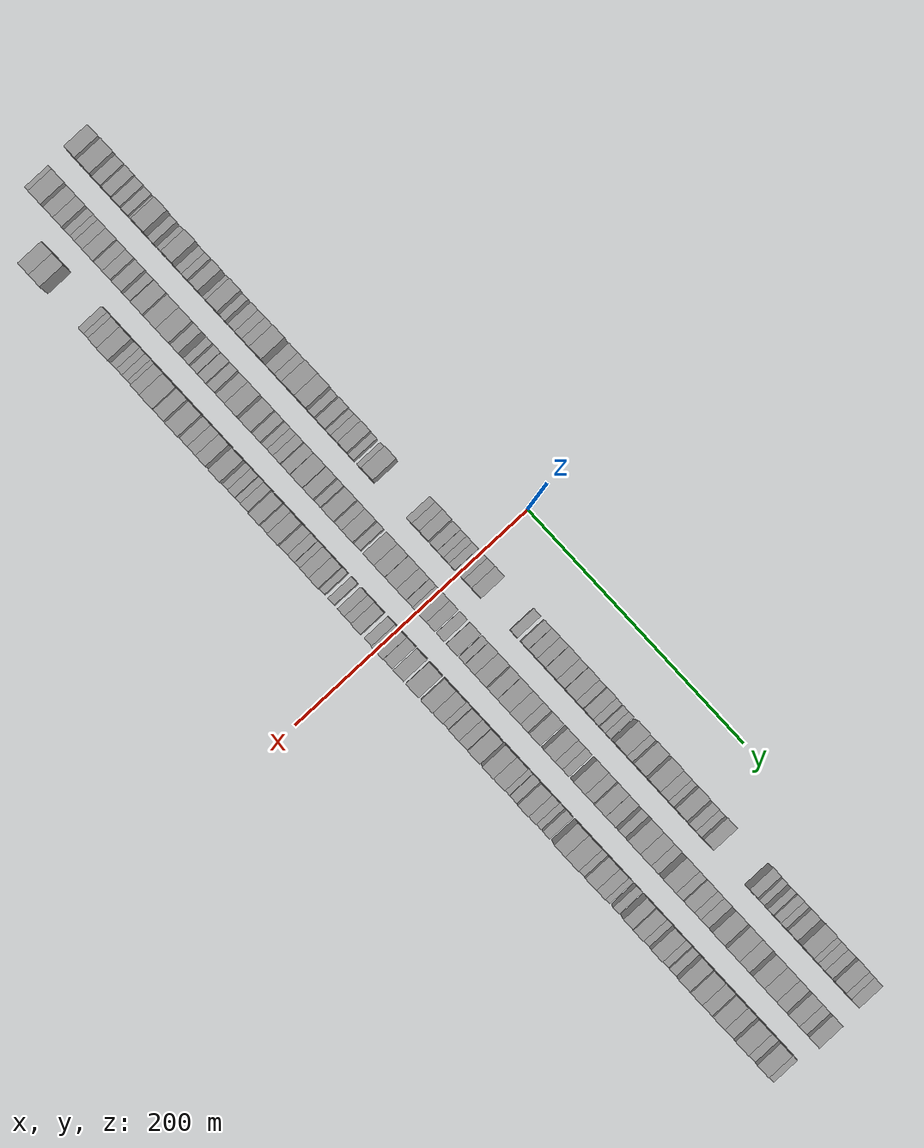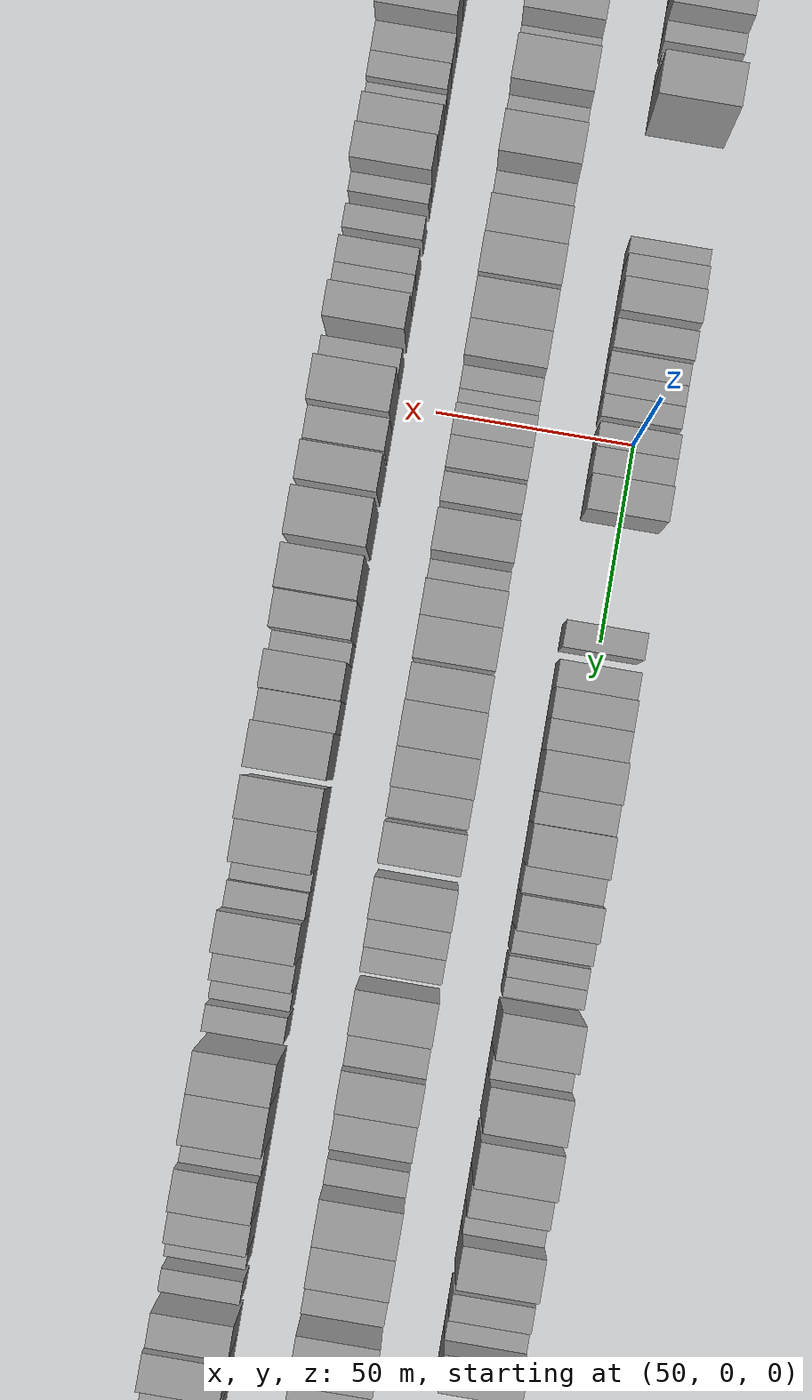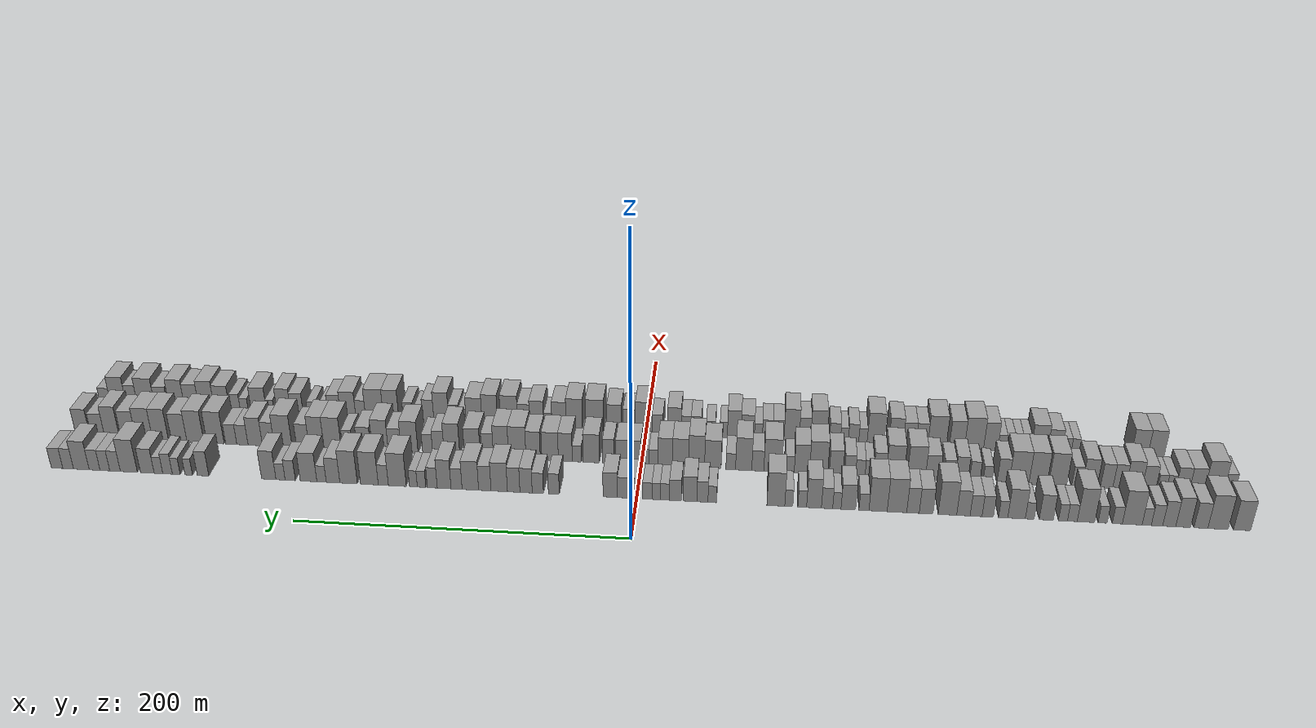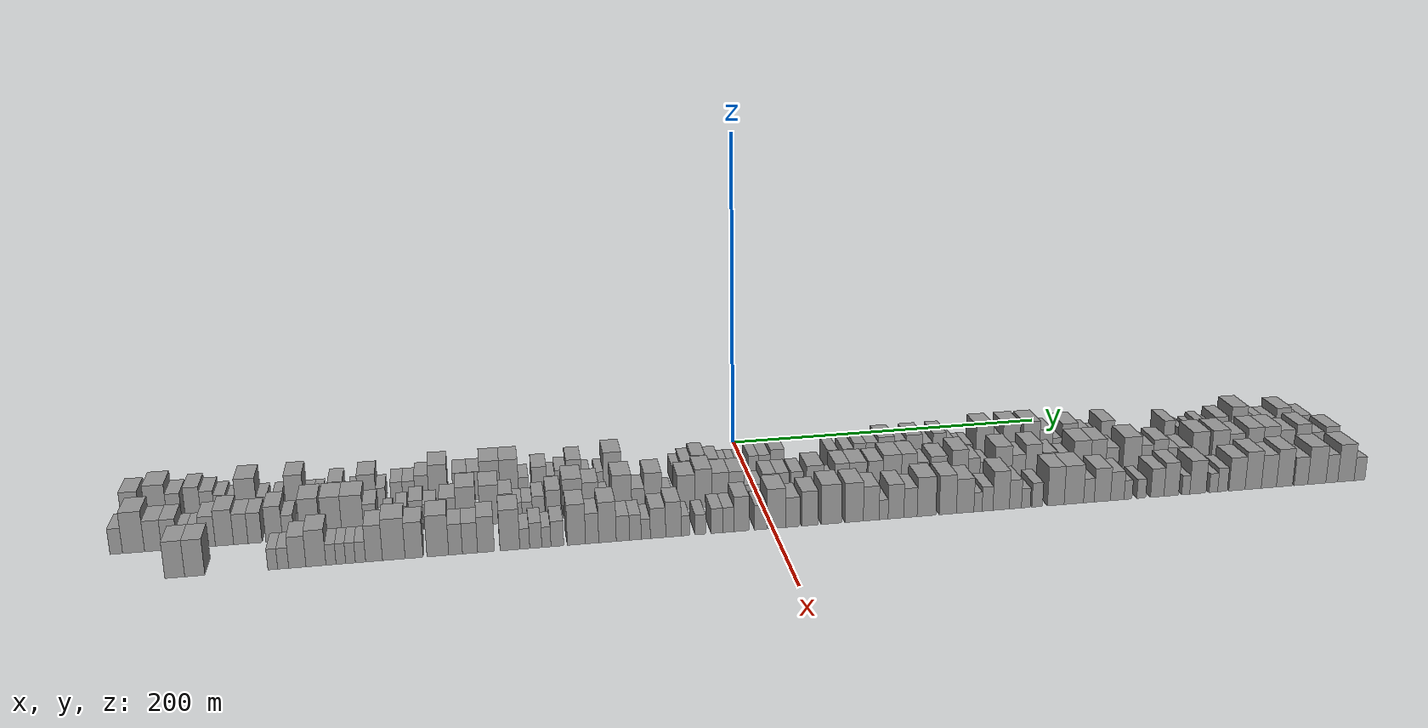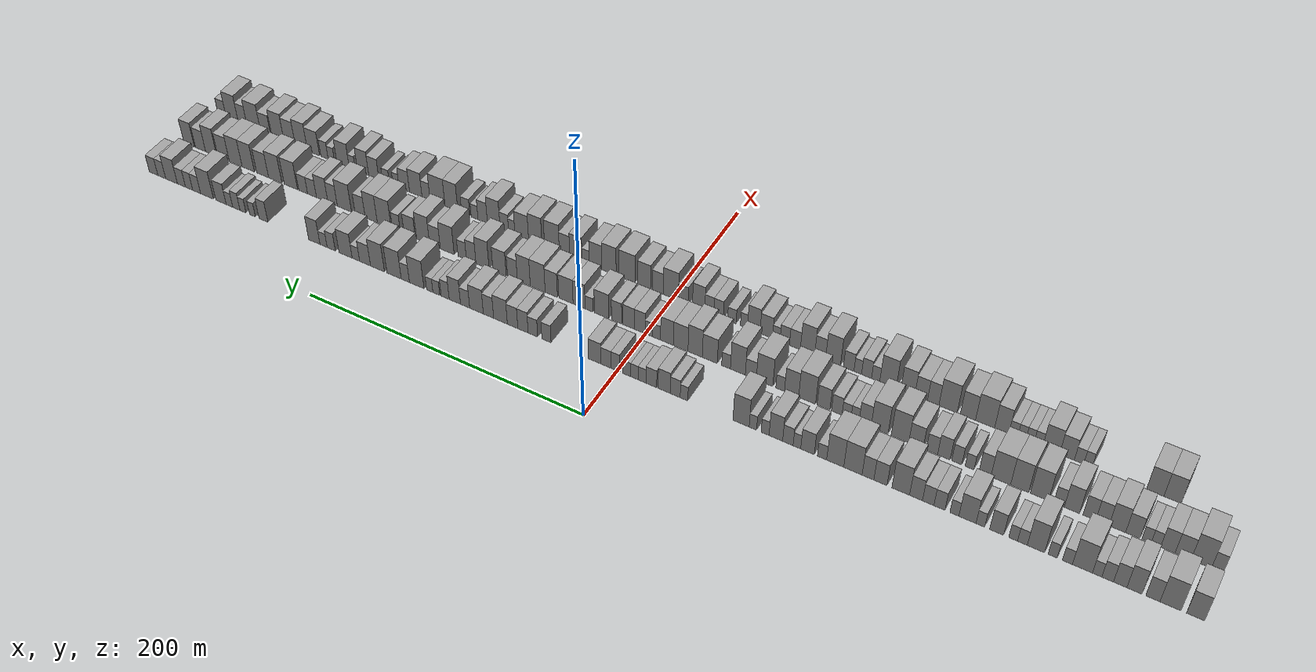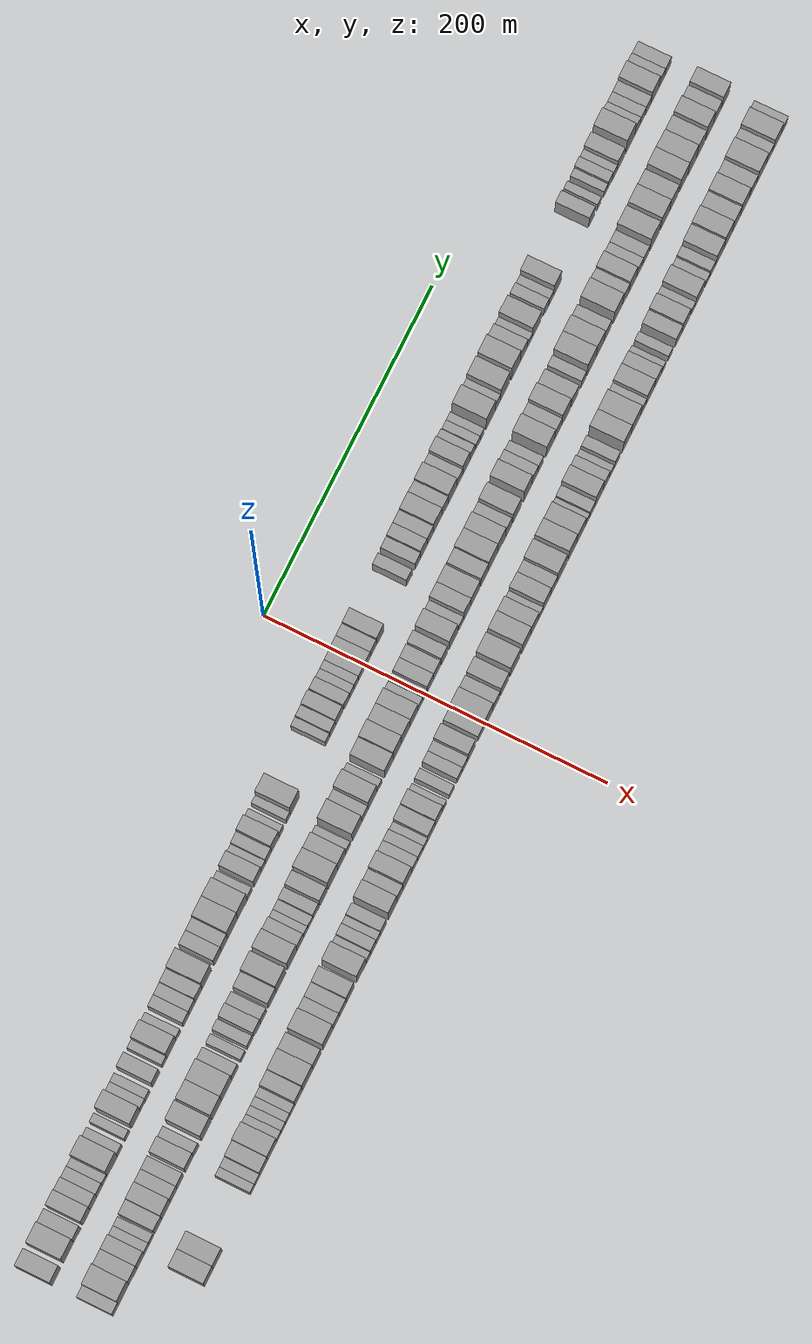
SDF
<sdf version="1.6">
 <world name="default">
  <scene>
   <sky><clouds><speed>12</speed></clouds></sky>
   <ambient>0.4 0.4 0.4 1</ambient>
   <background>0.7 0.7 0.7 1</background>
   <shadows>1</shadows>
  </scene>
  <gravity>0 0 -9.8066</gravity>
  <magnetic_field>6e-06 2.3e-05 -4.2e-05</magnetic_field>
  <physics default="0" name="default_physics" type="ode">
   <ode>
    <solver>
     <type>quick</type>
     <iters>10</iters>
     <sor>1.0</sor>
     <use_dynamic_moi_rescaling>0</use_dynamic_moi_rescaling>
    </solver>
    <constraints>
     <cfm>0</cfm>
     <erp>0.2</erp>
     <contact_max_correcting_vel>100</contact_max_correcting_vel>
     <contact_surface_layer>0.001</contact_surface_layer>
    </constraints>
   </ode>
   <max_step_size>0.004</max_step_size>
   <real_time_factor>1</real_time_factor>
   <real_time_update_rate>250</real_time_update_rate>
  </physics>
  <light name="sun" type="directional">
   <pose>0 0 10 0 0 0</pose>
   <diffuse>0.8 0.8 0.8 1</diffuse>
   <specular>0.2 0.2 0.2 1</specular>
   <attenuation>
    <range>1000</range>
    <constant>0.9</constant>
    <linear>0.01</linear>
    <quadratic>0.001</quadratic>
   </attenuation>
   <direction>-0.5 0.1 -0.9</direction>
  </light>
  <model name="building_1">
   <static>1</static>
   <pose>50.0000 -355.1001 0 0.000000 0.000000 0.000000</pose>
   <link name="link">
    <pose>0 0 10.50 0 0 0</pose>
    <collision name="collision"><geometry><box><size>20.0000 9.7997 21.0000</size></box></geometry></collision>
    <visual name="visual">
     <cast_shadows>0</cast_shadows>
     <geometry><box><size>20.0000 9.7997 21.0000</size></box></geometry>
     <material>
      <script>
       <uri>model://grey_wall/materials/scripts</uri>
       <uri>model://grey_wall/materials/textures</uri>
       <name>vrc/grey_wall</name>
      </script>
     </material>
    </visual>
   </link>
  </model>
  <model name="building_2">
   <static>1</static>
   <pose>50.0000 -341.4045 0 0.000000 0.000000 0.000000</pose>
   <link name="link">
    <pose>0 0 12.00 0 0 0</pose>
    <collision name="collision"><geometry><box><size>20.0000 11.5914 24.0000</size></box></geometry></collision>
    <visual name="visual">
     <cast_shadows>0</cast_shadows>
     <geometry><box><size>20.0000 11.5914 24.0000</size></box></geometry>
     <material>
      <script>
       <uri>model://grey_wall/materials/scripts</uri>
       <uri>model://grey_wall/materials/textures</uri>
       <name>vrc/grey_wall</name>
      </script>
     </material>
    </visual>
   </link>
  </model>
  <model name="building_3">
   <static>1</static>
   <pose>50.0000 -331.6680 0 0.000000 0.000000 0.000000</pose>
   <link name="link">
    <pose>0 0 9.00 0 0 0</pose>
    <collision name="collision"><geometry><box><size>20.0000 7.8818 18.0000</size></box></geometry></collision>
    <visual name="visual">
     <cast_shadows>0</cast_shadows>
     <geometry><box><size>20.0000 7.8818 18.0000</size></box></geometry>
     <material>
      <script>
       <uri>model://grey_wall/materials/scripts</uri>
       <uri>model://grey_wall/materials/textures</uri>
       <name>vrc/grey_wall</name>
      </script>
     </material>
    </visual>
   </link>
  </model>
  <model name="building_4">
   <static>1</static>
   <pose>50.0000 -321.4947 0 0.000000 0.000000 0.000000</pose>
   <link name="link">
    <pose>0 0 10.50 0 0 0</pose>
    <collision name="collision"><geometry><box><size>20.0000 8.4648 21.0000</size></box></geometry></collision>
    <visual name="visual">
     <cast_shadows>0</cast_shadows>
     <geometry><box><size>20.0000 8.4648 21.0000</size></box></geometry>
     <material>
      <script>
       <uri>model://grey_wall/materials/scripts</uri>
       <uri>model://grey_wall/materials/textures</uri>
       <name>vrc/grey_wall</name>
      </script>
     </material>
    </visual>
   </link>
  </model>
  <model name="building_5">
   <static>1</static>
   <pose>50.0000 -313.5152 0 0.000000 0.000000 0.000000</pose>
   <link name="link">
    <pose>0 0 9.00 0 0 0</pose>
    <collision name="collision"><geometry><box><size>20.0000 7.4942 18.0000</size></box></geometry></collision>
    <visual name="visual">
     <cast_shadows>0</cast_shadows>
     <geometry><box><size>20.0000 7.4942 18.0000</size></box></geometry>
     <material>
      <script>
       <uri>model://grey_wall/materials/scripts</uri>
       <uri>model://grey_wall/materials/textures</uri>
       <name>vrc/grey_wall</name>
      </script>
     </material>
    </visual>
   </link>
  </model>
  <model name="building_6">
   <static>1</static>
   <pose>50.0000 -306.5093 0 0.000000 0.000000 0.000000</pose>
   <link name="link">
    <pose>0 0 7.50 0 0 0</pose>
    <collision name="collision"><geometry><box><size>20.0000 6.5176 15.0000</size></box></geometry></collision>
    <visual name="visual">
     <cast_shadows>0</cast_shadows>
     <geometry><box><size>20.0000 6.5176 15.0000</size></box></geometry>
     <material>
      <script>
       <uri>model://grey_wall/materials/scripts</uri>
       <uri>model://grey_wall/materials/textures</uri>
       <name>vrc/grey_wall</name>
      </script>
     </material>
    </visual>
   </link>
  </model>
  <model name="building_7">
   <static>1</static>
   <pose>50.0000 -300.6045 0 0.000000 0.000000 0.000000</pose>
   <link name="link">
    <pose>0 0 6.00 0 0 0</pose>
    <collision name="collision"><geometry><box><size>20.0000 5.2920 12.0000</size></box></geometry></collision>
    <visual name="visual">
     <cast_shadows>0</cast_shadows>
     <geometry><box><size>20.0000 5.2920 12.0000</size></box></geometry>
     <material>
      <script>
       <uri>model://grey_wall/materials/scripts</uri>
       <uri>model://grey_wall/materials/textures</uri>
       <name>vrc/grey_wall</name>
      </script>
     </material>
    </visual>
   </link>
  </model>
  <model name="building_8">
   <static>1</static>
   <pose>50.0000 -292.2646 0 0.000000 0.000000 0.000000</pose>
   <link name="link">
    <pose>0 0 12.00 0 0 0</pose>
    <collision name="collision"><geometry><box><size>20.0000 11.3878 24.0000</size></box></geometry></collision>
    <visual name="visual">
     <cast_shadows>0</cast_shadows>
     <geometry><box><size>20.0000 11.3878 24.0000</size></box></geometry>
     <material>
      <script>
       <uri>model://grey_wall/materials/scripts</uri>
       <uri>model://grey_wall/materials/textures</uri>
       <name>vrc/grey_wall</name>
      </script>
     </material>
    </visual>
   </link>
  </model>
  <model name="building_9">
   <static>1</static>
   <pose>50.0000 -283.6906 0 0.000000 0.000000 0.000000</pose>
   <link name="link">
    <pose>0 0 6.00 0 0 0</pose>
    <collision name="collision"><geometry><box><size>20.0000 5.7602 12.0000</size></box></geometry></collision>
    <visual name="visual">
     <cast_shadows>0</cast_shadows>
     <geometry><box><size>20.0000 5.7602 12.0000</size></box></geometry>
     <material>
      <script>
       <uri>model://grey_wall/materials/scripts</uri>
       <uri>model://grey_wall/materials/textures</uri>
       <name>vrc/grey_wall</name>
      </script>
     </material>
    </visual>
   </link>
  </model>
  <model name="building_10">
   <static>1</static>
   <pose>50.0000 -275.2085 0 0.000000 0.000000 0.000000</pose>
   <link name="link">
    <pose>0 0 6.00 0 0 0</pose>
    <collision name="collision"><geometry><box><size>20.0000 5.2040 12.0000</size></box></geometry></collision>
    <visual name="visual">
     <cast_shadows>0</cast_shadows>
     <geometry><box><size>20.0000 5.2040 12.0000</size></box></geometry>
     <material>
      <script>
       <uri>model://grey_wall/materials/scripts</uri>
       <uri>model://grey_wall/materials/textures</uri>
       <name>vrc/grey_wall</name>
      </script>
     </material>
    </visual>
   </link>
  </model>
  <model name="building_11">
   <static>1</static>
   <pose>50.0000 -265.5791 0 0.000000 0.000000 0.000000</pose>
   <link name="link">
    <pose>0 0 12.00 0 0 0</pose>
    <collision name="collision"><geometry><box><size>20.0000 10.0548 24.0000</size></box></geometry></collision>
    <visual name="visual">
     <cast_shadows>0</cast_shadows>
     <geometry><box><size>20.0000 10.0548 24.0000</size></box></geometry>
     <material>
      <script>
       <uri>model://grey_wall/materials/scripts</uri>
       <uri>model://grey_wall/materials/textures</uri>
       <name>vrc/grey_wall</name>
      </script>
     </material>
    </visual>
   </link>
  </model>
  <model name="building_12">
   <static>1</static>
   <pose>50.0000 -257.7121 0 0.000000 0.000000 0.000000</pose>
   <link name="link">
    <pose>0 0 6.00 0 0 0</pose>
    <collision name="collision"><geometry><box><size>20.0000 5.6793 12.0000</size></box></geometry></collision>
    <visual name="visual">
     <cast_shadows>0</cast_shadows>
     <geometry><box><size>20.0000 5.6793 12.0000</size></box></geometry>
     <material>
      <script>
       <uri>model://grey_wall/materials/scripts</uri>
       <uri>model://grey_wall/materials/textures</uri>
       <name>vrc/grey_wall</name>
      </script>
     </material>
    </visual>
   </link>
  </model>
  <model name="building_13">
   <static>1</static>
   <pose>50.0000 -252.2907 0 0.000000 0.000000 0.000000</pose>
   <link name="link">
    <pose>0 0 6.00 0 0 0</pose>
    <collision name="collision"><geometry><box><size>20.0000 5.1635 12.0000</size></box></geometry></collision>
    <visual name="visual">
     <cast_shadows>0</cast_shadows>
     <geometry><box><size>20.0000 5.1635 12.0000</size></box></geometry>
     <material>
      <script>
       <uri>model://grey_wall/materials/scripts</uri>
       <uri>model://grey_wall/materials/textures</uri>
       <name>vrc/grey_wall</name>
      </script>
     </material>
    </visual>
   </link>
  </model>
  <model name="building_14">
   <static>1</static>
   <pose>50.0000 -242.6086 0 0.000000 0.000000 0.000000</pose>
   <link name="link">
    <pose>0 0 9.00 0 0 0</pose>
    <collision name="collision"><geometry><box><size>20.0000 8.2007 18.0000</size></box></geometry></collision>
    <visual name="visual">
     <cast_shadows>0</cast_shadows>
     <geometry><box><size>20.0000 8.2007 18.0000</size></box></geometry>
     <material>
      <script>
       <uri>model://grey_wall/materials/scripts</uri>
       <uri>model://grey_wall/materials/textures</uri>
       <name>vrc/grey_wall</name>
      </script>
     </material>
    </visual>
   </link>
  </model>
  <model name="building_15">
   <static>1</static>
   <pose>50.0000 -232.9550 0 0.000000 0.000000 0.000000</pose>
   <link name="link">
    <pose>0 0 6.00 0 0 0</pose>
    <collision name="collision"><geometry><box><size>20.0000 5.1066 12.0000</size></box></geometry></collision>
    <visual name="visual">
     <cast_shadows>0</cast_shadows>
     <geometry><box><size>20.0000 5.1066 12.0000</size></box></geometry>
     <material>
      <script>
       <uri>model://grey_wall/materials/scripts</uri>
       <uri>model://grey_wall/materials/textures</uri>
       <name>vrc/grey_wall</name>
      </script>
     </material>
    </visual>
   </link>
  </model>
  <model name="building_16">
   <static>1</static>
   <pose>50.0000 -225.2877 0 0.000000 0.000000 0.000000</pose>
   <link name="link">
    <pose>0 0 10.50 0 0 0</pose>
    <collision name="collision"><geometry><box><size>20.0000 10.2279 21.0000</size></box></geometry></collision>
    <visual name="visual">
     <cast_shadows>0</cast_shadows>
     <geometry><box><size>20.0000 10.2279 21.0000</size></box></geometry>
     <material>
      <script>
       <uri>model://grey_wall/materials/scripts</uri>
       <uri>model://grey_wall/materials/textures</uri>
       <name>vrc/grey_wall</name>
      </script>
     </material>
    </visual>
   </link>
  </model>
  <model name="building_17">
   <static>1</static>
   <pose>50.0000 -217.4994 0 0.000000 0.000000 0.000000</pose>
   <link name="link">
    <pose>0 0 6.00 0 0 0</pose>
    <collision name="collision"><geometry><box><size>20.0000 5.3487 12.0000</size></box></geometry></collision>
    <visual name="visual">
     <cast_shadows>0</cast_shadows>
     <geometry><box><size>20.0000 5.3487 12.0000</size></box></geometry>
     <material>
      <script>
       <uri>model://grey_wall/materials/scripts</uri>
       <uri>model://grey_wall/materials/textures</uri>
       <name>vrc/grey_wall</name>
      </script>
     </material>
    </visual>
   </link>
  </model>
  <model name="building_18">
   <static>1</static>
   <pose>50.0000 -208.4923 0 0.000000 0.000000 0.000000</pose>
   <link name="link">
    <pose>0 0 7.50 0 0 0</pose>
    <collision name="collision"><geometry><box><size>20.0000 6.6655 15.0000</size></box></geometry></collision>
    <visual name="visual">
     <cast_shadows>0</cast_shadows>
     <geometry><box><size>20.0000 6.6655 15.0000</size></box></geometry>
     <material>
      <script>
       <uri>model://grey_wall/materials/scripts</uri>
       <uri>model://grey_wall/materials/textures</uri>
       <name>vrc/grey_wall</name>
      </script>
     </material>
    </visual>
   </link>
  </model>
  <model name="building_19">
   <static>1</static>
   <pose>50.0000 -201.6772 0 0.000000 0.000000 0.000000</pose>
   <link name="link">
    <pose>0 0 7.50 0 0 0</pose>
    <collision name="collision"><geometry><box><size>20.0000 6.9646 15.0000</size></box></geometry></collision>
    <visual name="visual">
     <cast_shadows>0</cast_shadows>
     <geometry><box><size>20.0000 6.9646 15.0000</size></box></geometry>
     <material>
      <script>
       <uri>model://grey_wall/materials/scripts</uri>
       <uri>model://grey_wall/materials/textures</uri>
       <name>vrc/grey_wall</name>
      </script>
     </material>
    </visual>
   </link>
  </model>
  <model name="building_20">
   <static>1</static>
   <pose>50.0000 -194.2766 0 0.000000 0.000000 0.000000</pose>
   <link name="link">
    <pose>0 0 9.00 0 0 0</pose>
    <collision name="collision"><geometry><box><size>20.0000 7.8367 18.0000</size></box></geometry></collision>
    <visual name="visual">
     <cast_shadows>0</cast_shadows>
     <geometry><box><size>20.0000 7.8367 18.0000</size></box></geometry>
     <material>
      <script>
       <uri>model://grey_wall/materials/scripts</uri>
       <uri>model://grey_wall/materials/textures</uri>
       <name>vrc/grey_wall</name>
      </script>
     </material>
    </visual>
   </link>
  </model>
  <model name="building_21">
   <static>1</static>
   <pose>50.0000 -184.9264 0 0.000000 0.000000 0.000000</pose>
   <link name="link">
    <pose>0 0 12.00 0 0 0</pose>
    <collision name="collision"><geometry><box><size>20.0000 10.8636 24.0000</size></box></geometry></collision>
    <visual name="visual">
     <cast_shadows>0</cast_shadows>
     <geometry><box><size>20.0000 10.8636 24.0000</size></box></geometry>
     <material>
      <script>
       <uri>model://grey_wall/materials/scripts</uri>
       <uri>model://grey_wall/materials/textures</uri>
       <name>vrc/grey_wall</name>
      </script>
     </material>
    </visual>
   </link>
  </model>
  <model name="building_22">
   <static>1</static>
   <pose>50.0000 -172.4275 0 0.000000 0.000000 0.000000</pose>
   <link name="link">
    <pose>0 0 9.00 0 0 0</pose>
    <collision name="collision"><geometry><box><size>20.0000 8.1343 18.0000</size></box></geometry></collision>
    <visual name="visual">
     <cast_shadows>0</cast_shadows>
     <geometry><box><size>20.0000 8.1343 18.0000</size></box></geometry>
     <material>
      <script>
       <uri>model://grey_wall/materials/scripts</uri>
       <uri>model://grey_wall/materials/textures</uri>
       <name>vrc/grey_wall</name>
      </script>
     </material>
    </visual>
   </link>
  </model>
  <model name="building_23">
   <static>1</static>
   <pose>50.0000 -164.6802 0 0.000000 0.000000 0.000000</pose>
   <link name="link">
    <pose>0 0 9.00 0 0 0</pose>
    <collision name="collision"><geometry><box><size>20.0000 7.3603 18.0000</size></box></geometry></collision>
    <visual name="visual">
     <cast_shadows>0</cast_shadows>
     <geometry><box><size>20.0000 7.3603 18.0000</size></box></geometry>
     <material>
      <script>
       <uri>model://grey_wall/materials/scripts</uri>
       <uri>model://grey_wall/materials/textures</uri>
       <name>vrc/grey_wall</name>
      </script>
     </material>
    </visual>
   </link>
  </model>
  <model name="building_24">
   <static>1</static>
   <pose>50.0000 -155.2501 0 0.000000 0.000000 0.000000</pose>
   <link name="link">
    <pose>0 0 12.00 0 0 0</pose>
    <collision name="collision"><geometry><box><size>20.0000 11.4999 24.0000</size></box></geometry></collision>
    <visual name="visual">
     <cast_shadows>0</cast_shadows>
     <geometry><box><size>20.0000 11.4999 24.0000</size></box></geometry>
     <material>
      <script>
       <uri>model://grey_wall/materials/scripts</uri>
       <uri>model://grey_wall/materials/textures</uri>
       <name>vrc/grey_wall</name>
      </script>
     </material>
    </visual>
   </link>
  </model>
  <model name="building_25">
   <static>1</static>
   <pose>50.0000 -144.0973 0 0.000000 0.000000 0.000000</pose>
   <link name="link">
    <pose>0 0 12.00 0 0 0</pose>
    <collision name="collision"><geometry><box><size>20.0000 10.8057 24.0000</size></box></geometry></collision>
    <visual name="visual">
     <cast_shadows>0</cast_shadows>
     <geometry><box><size>20.0000 10.8057 24.0000</size></box></geometry>
     <material>
      <script>
       <uri>model://grey_wall/materials/scripts</uri>
       <uri>model://grey_wall/materials/textures</uri>
       <name>vrc/grey_wall</name>
      </script>
     </material>
    </visual>
   </link>
  </model>
  <model name="building_26">
   <static>1</static>
   <pose>50.0000 -135.7476 0 0.000000 0.000000 0.000000</pose>
   <link name="link">
    <pose>0 0 6.00 0 0 0</pose>
    <collision name="collision"><geometry><box><size>20.0000 5.8939 12.0000</size></box></geometry></collision>
    <visual name="visual">
     <cast_shadows>0</cast_shadows>
     <geometry><box><size>20.0000 5.8939 12.0000</size></box></geometry>
     <material>
      <script>
       <uri>model://grey_wall/materials/scripts</uri>
       <uri>model://grey_wall/materials/textures</uri>
       <name>vrc/grey_wall</name>
      </script>
     </material>
    </visual>
   </link>
  </model>
  <model name="building_27">
   <static>1</static>
   <pose>50.0000 -126.4780 0 0.000000 0.000000 0.000000</pose>
   <link name="link">
    <pose>0 0 9.00 0 0 0</pose>
    <collision name="collision"><geometry><box><size>20.0000 8.6452 18.0000</size></box></geometry></collision>
    <visual name="visual">
     <cast_shadows>0</cast_shadows>
     <geometry><box><size>20.0000 8.6452 18.0000</size></box></geometry>
     <material>
      <script>
       <uri>model://grey_wall/materials/scripts</uri>
       <uri>model://grey_wall/materials/textures</uri>
       <name>vrc/grey_wall</name>
      </script>
     </material>
    </visual>
   </link>
  </model>
  <model name="building_28">
   <static>1</static>
   <pose>50.0000 -119.6944 0 0.000000 0.000000 0.000000</pose>
   <link name="link">
    <pose>0 0 6.00 0 0 0</pose>
    <collision name="collision"><geometry><box><size>20.0000 4.9221 12.0000</size></box></geometry></collision>
    <visual name="visual">
     <cast_shadows>0</cast_shadows>
     <geometry><box><size>20.0000 4.9221 12.0000</size></box></geometry>
     <material>
      <script>
       <uri>model://grey_wall/materials/scripts</uri>
       <uri>model://grey_wall/materials/textures</uri>
       <name>vrc/grey_wall</name>
      </script>
     </material>
    </visual>
   </link>
  </model>
  <model name="building_29">
   <static>1</static>
   <pose>50.0000 -113.8767 0 0.000000 0.000000 0.000000</pose>
   <link name="link">
    <pose>0 0 7.50 0 0 0</pose>
    <collision name="collision"><geometry><box><size>20.0000 6.7132 15.0000</size></box></geometry></collision>
    <visual name="visual">
     <cast_shadows>0</cast_shadows>
     <geometry><box><size>20.0000 6.7132 15.0000</size></box></geometry>
     <material>
      <script>
       <uri>model://grey_wall/materials/scripts</uri>
       <uri>model://grey_wall/materials/textures</uri>
       <name>vrc/grey_wall</name>
      </script>
     </material>
    </visual>
   </link>
  </model>
  <model name="building_30">
   <static>1</static>
   <pose>50.0000 -106.1210 0 0.000000 0.000000 0.000000</pose>
   <link name="link">
    <pose>0 0 10.50 0 0 0</pose>
    <collision name="collision"><geometry><box><size>20.0000 8.7982 21.0000</size></box></geometry></collision>
    <visual name="visual">
     <cast_shadows>0</cast_shadows>
     <geometry><box><size>20.0000 8.7982 21.0000</size></box></geometry>
     <material>
      <script>
       <uri>model://grey_wall/materials/scripts</uri>
       <uri>model://grey_wall/materials/textures</uri>
       <name>vrc/grey_wall</name>
      </script>
     </material>
    </visual>
   </link>
  </model>
  <model name="building_31">
   <static>1</static>
   <pose>50.0000 -99.1354 0 0.000000 0.000000 0.000000</pose>
   <link name="link">
    <pose>0 0 6.00 0 0 0</pose>
    <collision name="collision"><geometry><box><size>20.0000 5.1730 12.0000</size></box></geometry></collision>
    <visual name="visual">
     <cast_shadows>0</cast_shadows>
     <geometry><box><size>20.0000 5.1730 12.0000</size></box></geometry>
     <material>
      <script>
       <uri>model://grey_wall/materials/scripts</uri>
       <uri>model://grey_wall/materials/textures</uri>
       <name>vrc/grey_wall</name>
      </script>
     </material>
    </visual>
   </link>
  </model>
  <model name="building_32">
   <static>1</static>
   <pose>50.0000 -91.1414 0 0.000000 0.000000 0.000000</pose>
   <link name="link">
    <pose>0 0 6.00 0 0 0</pose>
    <collision name="collision"><geometry><box><size>20.0000 4.8150 12.0000</size></box></geometry></collision>
    <visual name="visual">
     <cast_shadows>0</cast_shadows>
     <geometry><box><size>20.0000 4.8150 12.0000</size></box></geometry>
     <material>
      <script>
       <uri>model://grey_wall/materials/scripts</uri>
       <uri>model://grey_wall/materials/textures</uri>
       <name>vrc/grey_wall</name>
      </script>
     </material>
    </visual>
   </link>
  </model>
  <model name="building_33">
   <static>1</static>
   <pose>50.0000 -83.4060 0 0.000000 0.000000 0.000000</pose>
   <link name="link">
    <pose>0 0 12.00 0 0 0</pose>
    <collision name="collision"><geometry><box><size>20.0000 10.6557 24.0000</size></box></geometry></collision>
    <visual name="visual">
     <cast_shadows>0</cast_shadows>
     <geometry><box><size>20.0000 10.6557 24.0000</size></box></geometry>
     <material>
      <script>
       <uri>model://grey_wall/materials/scripts</uri>
       <uri>model://grey_wall/materials/textures</uri>
       <name>vrc/grey_wall</name>
      </script>
     </material>
    </visual>
   </link>
  </model>
  <model name="building_34">
   <static>1</static>
   <pose>50.0000 -45.3212 0 0.000000 0.000000 0.000000</pose>
   <link name="link">
    <pose>0 0 6.00 0 0 0</pose>
    <collision name="collision"><geometry><box><size>20.0000 5.1713 12.0000</size></box></geometry></collision>
    <visual name="visual">
     <cast_shadows>0</cast_shadows>
     <geometry><box><size>20.0000 5.1713 12.0000</size></box></geometry>
     <material>
      <script>
       <uri>model://grey_wall/materials/scripts</uri>
       <uri>model://grey_wall/materials/textures</uri>
       <name>vrc/grey_wall</name>
      </script>
     </material>
    </visual>
   </link>
  </model>
  <model name="building_35">
   <static>1</static>
   <pose>50.0000 -39.4127 0 0.000000 0.000000 0.000000</pose>
   <link name="link">
    <pose>0 0 7.50 0 0 0</pose>
    <collision name="collision"><geometry><box><size>20.0000 6.6456 15.0000</size></box></geometry></collision>
    <visual name="visual">
     <cast_shadows>0</cast_shadows>
     <geometry><box><size>20.0000 6.6456 15.0000</size></box></geometry>
     <material>
      <script>
       <uri>model://grey_wall/materials/scripts</uri>
       <uri>model://grey_wall/materials/textures</uri>
       <name>vrc/grey_wall</name>
      </script>
     </material>
    </visual>
   </link>
  </model>
  <model name="building_36">
   <static>1</static>
   <pose>50.0000 -31.9131 0 0.000000 0.000000 0.000000</pose>
   <link name="link">
    <pose>0 0 9.00 0 0 0</pose>
    <collision name="collision"><geometry><box><size>20.0000 8.3536 18.0000</size></box></geometry></collision>
    <visual name="visual">
     <cast_shadows>0</cast_shadows>
     <geometry><box><size>20.0000 8.3536 18.0000</size></box></geometry>
     <material>
      <script>
       <uri>model://grey_wall/materials/scripts</uri>
       <uri>model://grey_wall/materials/textures</uri>
       <name>vrc/grey_wall</name>
      </script>
     </material>
    </visual>
   </link>
  </model>
  <model name="building_37">
   <static>1</static>
   <pose>50.0000 -23.1117 0 0.000000 0.000000 0.000000</pose>
   <link name="link">
    <pose>0 0 7.50 0 0 0</pose>
    <collision name="collision"><geometry><box><size>20.0000 7.2491 15.0000</size></box></geometry></collision>
    <visual name="visual">
     <cast_shadows>0</cast_shadows>
     <geometry><box><size>20.0000 7.2491 15.0000</size></box></geometry>
     <material>
      <script>
       <uri>model://grey_wall/materials/scripts</uri>
       <uri>model://grey_wall/materials/textures</uri>
       <name>vrc/grey_wall</name>
      </script>
     </material>
    </visual>
   </link>
  </model>
  <model name="building_38">
   <static>1</static>
   <pose>50.0000 -16.7478 0 0.000000 0.000000 0.000000</pose>
   <link name="link">
    <pose>0 0 6.00 0 0 0</pose>
    <collision name="collision"><geometry><box><size>20.0000 5.4787 12.0000</size></box></geometry></collision>
    <visual name="visual">
     <cast_shadows>0</cast_shadows>
     <geometry><box><size>20.0000 5.4787 12.0000</size></box></geometry>
     <material>
      <script>
       <uri>model://grey_wall/materials/scripts</uri>
       <uri>model://grey_wall/materials/textures</uri>
       <name>vrc/grey_wall</name>
      </script>
     </material>
    </visual>
   </link>
  </model>
  <model name="building_39">
   <static>1</static>
   <pose>50.0000 -11.4639 0 0.000000 0.000000 0.000000</pose>
   <link name="link">
    <pose>0 0 6.00 0 0 0</pose>
    <collision name="collision"><geometry><box><size>20.0000 5.0892 12.0000</size></box></geometry></collision>
    <visual name="visual">
     <cast_shadows>0</cast_shadows>
     <geometry><box><size>20.0000 5.0892 12.0000</size></box></geometry>
     <material>
      <script>
       <uri>model://grey_wall/materials/scripts</uri>
       <uri>model://grey_wall/materials/textures</uri>
       <name>vrc/grey_wall</name>
      </script>
     </material>
    </visual>
   </link>
  </model>
  <model name="building_40">
   <static>1</static>
   <pose>50.0000 -6.0964 0 0.000000 0.000000 0.000000</pose>
   <link name="link">
    <pose>0 0 6.00 0 0 0</pose>
    <collision name="collision"><geometry><box><size>20.0000 5.6457 12.0000</size></box></geometry></collision>
    <visual name="visual">
     <cast_shadows>0</cast_shadows>
     <geometry><box><size>20.0000 5.6457 12.0000</size></box></geometry>
     <material>
      <script>
       <uri>model://grey_wall/materials/scripts</uri>
       <uri>model://grey_wall/materials/textures</uri>
       <name>vrc/grey_wall</name>
      </script>
     </material>
    </visual>
   </link>
  </model>
  <model name="building_41">
   <static>1</static>
   <pose>50.0000 1.7427 0 0.000000 0.000000 0.000000</pose>
   <link name="link">
    <pose>0 0 7.50 0 0 0</pose>
    <collision name="collision"><geometry><box><size>20.0000 6.0325 15.0000</size></box></geometry></collision>
    <visual name="visual">
     <cast_shadows>0</cast_shadows>
     <geometry><box><size>20.0000 6.0325 15.0000</size></box></geometry>
     <material>
      <script>
       <uri>model://grey_wall/materials/scripts</uri>
       <uri>model://grey_wall/materials/textures</uri>
       <name>vrc/grey_wall</name>
      </script>
     </material>
    </visual>
   </link>
  </model>
  <model name="building_42">
   <static>1</static>
   <pose>50.0000 8.3650 0 0.000000 0.000000 0.000000</pose>
   <link name="link">
    <pose>0 0 7.50 0 0 0</pose>
    <collision name="collision"><geometry><box><size>20.0000 7.2120 15.0000</size></box></geometry></collision>
    <visual name="visual">
     <cast_shadows>0</cast_shadows>
     <geometry><box><size>20.0000 7.2120 15.0000</size></box></geometry>
     <material>
      <script>
       <uri>model://grey_wall/materials/scripts</uri>
       <uri>model://grey_wall/materials/textures</uri>
       <name>vrc/grey_wall</name>
      </script>
     </material>
    </visual>
   </link>
  </model>
  <model name="building_43">
   <static>1</static>
   <pose>50.0000 16.3239 0 0.000000 0.000000 0.000000</pose>
   <link name="link">
    <pose>0 0 9.00 0 0 0</pose>
    <collision name="collision"><geometry><box><size>20.0000 8.7058 18.0000</size></box></geometry></collision>
    <visual name="visual">
     <cast_shadows>0</cast_shadows>
     <geometry><box><size>20.0000 8.7058 18.0000</size></box></geometry>
     <material>
      <script>
       <uri>model://grey_wall/materials/scripts</uri>
       <uri>model://grey_wall/materials/textures</uri>
       <name>vrc/grey_wall</name>
      </script>
     </material>
    </visual>
   </link>
  </model>
  <model name="building_44">
   <static>1</static>
   <pose>50.0000 50.6736 0 0.000000 0.000000 0.000000</pose>
   <link name="link">
    <pose>0 0 7.50 0 0 0</pose>
    <collision name="collision"><geometry><box><size>20.0000 6.6645 15.0000</size></box></geometry></collision>
    <visual name="visual">
     <cast_shadows>0</cast_shadows>
     <geometry><box><size>20.0000 6.6645 15.0000</size></box></geometry>
     <material>
      <script>
       <uri>model://grey_wall/materials/scripts</uri>
       <uri>model://grey_wall/materials/textures</uri>
       <name>vrc/grey_wall</name>
      </script>
     </material>
    </visual>
   </link>
  </model>
  <model name="building_45">
   <static>1</static>
   <pose>50.0000 60.4581 0 0.000000 0.000000 0.000000</pose>
   <link name="link">
    <pose>0 0 7.50 0 0 0</pose>
    <collision name="collision"><geometry><box><size>20.0000 6.9047 15.0000</size></box></geometry></collision>
    <visual name="visual">
     <cast_shadows>0</cast_shadows>
     <geometry><box><size>20.0000 6.9047 15.0000</size></box></geometry>
     <material>
      <script>
       <uri>model://grey_wall/materials/scripts</uri>
       <uri>model://grey_wall/materials/textures</uri>
       <name>vrc/grey_wall</name>
      </script>
     </material>
    </visual>
   </link>
  </model>
  <model name="building_46">
   <static>1</static>
   <pose>50.0000 67.6702 0 0.000000 0.000000 0.000000</pose>
   <link name="link">
    <pose>0 0 9.00 0 0 0</pose>
    <collision name="collision"><geometry><box><size>20.0000 7.5195 18.0000</size></box></geometry></collision>
    <visual name="visual">
     <cast_shadows>0</cast_shadows>
     <geometry><box><size>20.0000 7.5195 18.0000</size></box></geometry>
     <material>
      <script>
       <uri>model://grey_wall/materials/scripts</uri>
       <uri>model://grey_wall/materials/textures</uri>
       <name>vrc/grey_wall</name>
      </script>
     </material>
    </visual>
   </link>
  </model>
  <model name="building_47">
   <static>1</static>
   <pose>50.0000 75.2635 0 0.000000 0.000000 0.000000</pose>
   <link name="link">
    <pose>0 0 9.00 0 0 0</pose>
    <collision name="collision"><geometry><box><size>20.0000 7.6672 18.0000</size></box></geometry></collision>
    <visual name="visual">
     <cast_shadows>0</cast_shadows>
     <geometry><box><size>20.0000 7.6672 18.0000</size></box></geometry>
     <material>
      <script>
       <uri>model://grey_wall/materials/scripts</uri>
       <uri>model://grey_wall/materials/textures</uri>
       <name>vrc/grey_wall</name>
      </script>
     </material>
    </visual>
   </link>
  </model>
  <model name="building_48">
   <static>1</static>
   <pose>50.0000 84.1313 0 0.000000 0.000000 0.000000</pose>
   <link name="link">
    <pose>0 0 10.50 0 0 0</pose>
    <collision name="collision"><geometry><box><size>20.0000 10.0684 21.0000</size></box></geometry></collision>
    <visual name="visual">
     <cast_shadows>0</cast_shadows>
     <geometry><box><size>20.0000 10.0684 21.0000</size></box></geometry>
     <material>
      <script>
       <uri>model://grey_wall/materials/scripts</uri>
       <uri>model://grey_wall/materials/textures</uri>
       <name>vrc/grey_wall</name>
      </script>
     </material>
    </visual>
   </link>
  </model>
  <model name="building_49">
   <static>1</static>
   <pose>50.0000 92.9879 0 0.000000 0.000000 0.000000</pose>
   <link name="link">
    <pose>0 0 9.00 0 0 0</pose>
    <collision name="collision"><geometry><box><size>20.0000 7.6447 18.0000</size></box></geometry></collision>
    <visual name="visual">
     <cast_shadows>0</cast_shadows>
     <geometry><box><size>20.0000 7.6447 18.0000</size></box></geometry>
     <material>
      <script>
       <uri>model://grey_wall/materials/scripts</uri>
       <uri>model://grey_wall/materials/textures</uri>
       <name>vrc/grey_wall</name>
      </script>
     </material>
    </visual>
   </link>
  </model>
  <model name="building_50">
   <static>1</static>
   <pose>50.0000 101.9029 0 0.000000 0.000000 0.000000</pose>
   <link name="link">
    <pose>0 0 10.50 0 0 0</pose>
    <collision name="collision"><geometry><box><size>20.0000 10.1852 21.0000</size></box></geometry></collision>
    <visual name="visual">
     <cast_shadows>0</cast_shadows>
     <geometry><box><size>20.0000 10.1852 21.0000</size></box></geometry>
     <material>
      <script>
       <uri>model://grey_wall/materials/scripts</uri>
       <uri>model://grey_wall/materials/textures</uri>
       <name>vrc/grey_wall</name>
      </script>
     </material>
    </visual>
   </link>
  </model>
  <model name="building_51">
   <static>1</static>
   <pose>50.0000 110.4043 0 0.000000 0.000000 0.000000</pose>
   <link name="link">
    <pose>0 0 7.50 0 0 0</pose>
    <collision name="collision"><geometry><box><size>20.0000 6.8177 15.0000</size></box></geometry></collision>
    <visual name="visual">
     <cast_shadows>0</cast_shadows>
     <geometry><box><size>20.0000 6.8177 15.0000</size></box></geometry>
     <material>
      <script>
       <uri>model://grey_wall/materials/scripts</uri>
       <uri>model://grey_wall/materials/textures</uri>
       <name>vrc/grey_wall</name>
      </script>
     </material>
    </visual>
   </link>
  </model>
  <model name="building_52">
   <static>1</static>
   <pose>50.0000 118.0858 0 0.000000 0.000000 0.000000</pose>
   <link name="link">
    <pose>0 0 10.50 0 0 0</pose>
    <collision name="collision"><geometry><box><size>20.0000 8.5454 21.0000</size></box></geometry></collision>
    <visual name="visual">
     <cast_shadows>0</cast_shadows>
     <geometry><box><size>20.0000 8.5454 21.0000</size></box></geometry>
     <material>
      <script>
       <uri>model://grey_wall/materials/scripts</uri>
       <uri>model://grey_wall/materials/textures</uri>
       <name>vrc/grey_wall</name>
      </script>
     </material>
    </visual>
   </link>
  </model>
  <model name="building_53">
   <static>1</static>
   <pose>50.0000 125.4102 0 0.000000 0.000000 0.000000</pose>
   <link name="link">
    <pose>0 0 7.50 0 0 0</pose>
    <collision name="collision"><geometry><box><size>20.0000 6.1034 15.0000</size></box></geometry></collision>
    <visual name="visual">
     <cast_shadows>0</cast_shadows>
     <geometry><box><size>20.0000 6.1034 15.0000</size></box></geometry>
     <material>
      <script>
       <uri>model://grey_wall/materials/scripts</uri>
       <uri>model://grey_wall/materials/textures</uri>
       <name>vrc/grey_wall</name>
      </script>
     </material>
    </visual>
   </link>
  </model>
  <model name="building_54">
   <static>1</static>
   <pose>50.0000 132.0772 0 0.000000 0.000000 0.000000</pose>
   <link name="link">
    <pose>0 0 6.00 0 0 0</pose>
    <collision name="collision"><geometry><box><size>20.0000 5.2305 12.0000</size></box></geometry></collision>
    <visual name="visual">
     <cast_shadows>0</cast_shadows>
     <geometry><box><size>20.0000 5.2305 12.0000</size></box></geometry>
     <material>
      <script>
       <uri>model://grey_wall/materials/scripts</uri>
       <uri>model://grey_wall/materials/textures</uri>
       <name>vrc/grey_wall</name>
      </script>
     </material>
    </visual>
   </link>
  </model>
  <model name="building_55">
   <static>1</static>
   <pose>50.0000 137.1034 0 0.000000 0.000000 0.000000</pose>
   <link name="link">
    <pose>0 0 6.00 0 0 0</pose>
    <collision name="collision"><geometry><box><size>20.0000 4.8220 12.0000</size></box></geometry></collision>
    <visual name="visual">
     <cast_shadows>0</cast_shadows>
     <geometry><box><size>20.0000 4.8220 12.0000</size></box></geometry>
     <material>
      <script>
       <uri>model://grey_wall/materials/scripts</uri>
       <uri>model://grey_wall/materials/textures</uri>
       <name>vrc/grey_wall</name>
      </script>
     </material>
    </visual>
   </link>
  </model>
  <model name="building_56">
   <static>1</static>
   <pose>50.0000 147.1012 0 0.000000 0.000000 0.000000</pose>
   <link name="link">
    <pose>0 0 12.00 0 0 0</pose>
    <collision name="collision"><geometry><box><size>20.0000 11.1736 24.0000</size></box></geometry></collision>
    <visual name="visual">
     <cast_shadows>0</cast_shadows>
     <geometry><box><size>20.0000 11.1736 24.0000</size></box></geometry>
     <material>
      <script>
       <uri>model://grey_wall/materials/scripts</uri>
       <uri>model://grey_wall/materials/textures</uri>
       <name>vrc/grey_wall</name>
      </script>
     </material>
    </visual>
   </link>
  </model>
  <model name="building_57">
   <static>1</static>
   <pose>50.0000 155.8276 0 0.000000 0.000000 0.000000</pose>
   <link name="link">
    <pose>0 0 7.50 0 0 0</pose>
    <collision name="collision"><geometry><box><size>20.0000 6.2790 15.0000</size></box></geometry></collision>
    <visual name="visual">
     <cast_shadows>0</cast_shadows>
     <geometry><box><size>20.0000 6.2790 15.0000</size></box></geometry>
     <material>
      <script>
       <uri>model://grey_wall/materials/scripts</uri>
       <uri>model://grey_wall/materials/textures</uri>
       <name>vrc/grey_wall</name>
      </script>
     </material>
    </visual>
   </link>
  </model>
  <model name="building_58">
   <static>1</static>
   <pose>50.0000 164.4789 0 0.000000 0.000000 0.000000</pose>
   <link name="link">
    <pose>0 0 12.00 0 0 0</pose>
    <collision name="collision"><geometry><box><size>20.0000 11.0237 24.0000</size></box></geometry></collision>
    <visual name="visual">
     <cast_shadows>0</cast_shadows>
     <geometry><box><size>20.0000 11.0237 24.0000</size></box></geometry>
     <material>
      <script>
       <uri>model://grey_wall/materials/scripts</uri>
       <uri>model://grey_wall/materials/textures</uri>
       <name>vrc/grey_wall</name>
      </script>
     </material>
    </visual>
   </link>
  </model>
  <model name="building_59">
   <static>1</static>
   <pose>50.0000 177.4538 0 0.000000 0.000000 0.000000</pose>
   <link name="link">
    <pose>0 0 12.00 0 0 0</pose>
    <collision name="collision"><geometry><box><size>20.0000 10.9261 24.0000</size></box></geometry></collision>
    <visual name="visual">
     <cast_shadows>0</cast_shadows>
     <geometry><box><size>20.0000 10.9261 24.0000</size></box></geometry>
     <material>
      <script>
       <uri>model://grey_wall/materials/scripts</uri>
       <uri>model://grey_wall/materials/textures</uri>
       <name>vrc/grey_wall</name>
      </script>
     </material>
    </visual>
   </link>
  </model>
  <model name="building_60">
   <static>1</static>
   <pose>50.0000 187.1808 0 0.000000 0.000000 0.000000</pose>
   <link name="link">
    <pose>0 0 9.00 0 0 0</pose>
    <collision name="collision"><geometry><box><size>20.0000 8.5278 18.0000</size></box></geometry></collision>
    <visual name="visual">
     <cast_shadows>0</cast_shadows>
     <geometry><box><size>20.0000 8.5278 18.0000</size></box></geometry>
     <material>
      <script>
       <uri>model://grey_wall/materials/scripts</uri>
       <uri>model://grey_wall/materials/textures</uri>
       <name>vrc/grey_wall</name>
      </script>
     </material>
    </visual>
   </link>
  </model>
  <model name="building_61">
   <static>1</static>
   <pose>50.0000 194.3775 0 0.000000 0.000000 0.000000</pose>
   <link name="link">
    <pose>0 0 6.00 0 0 0</pose>
    <collision name="collision"><geometry><box><size>20.0000 5.8655 12.0000</size></box></geometry></collision>
    <visual name="visual">
     <cast_shadows>0</cast_shadows>
     <geometry><box><size>20.0000 5.8655 12.0000</size></box></geometry>
     <material>
      <script>
       <uri>model://grey_wall/materials/scripts</uri>
       <uri>model://grey_wall/materials/textures</uri>
       <name>vrc/grey_wall</name>
      </script>
     </material>
    </visual>
   </link>
  </model>
  <model name="building_62">
   <static>1</static>
   <pose>50.0000 202.5388 0 0.000000 0.000000 0.000000</pose>
   <link name="link">
    <pose>0 0 10.50 0 0 0</pose>
    <collision name="collision"><geometry><box><size>20.0000 10.4572 21.0000</size></box></geometry></collision>
    <visual name="visual">
     <cast_shadows>0</cast_shadows>
     <geometry><box><size>20.0000 10.4572 21.0000</size></box></geometry>
     <material>
      <script>
       <uri>model://grey_wall/materials/scripts</uri>
       <uri>model://grey_wall/materials/textures</uri>
       <name>vrc/grey_wall</name>
      </script>
     </material>
    </visual>
   </link>
  </model>
  <model name="building_63">
   <static>1</static>
   <pose>50.0000 214.0014 0 0.000000 0.000000 0.000000</pose>
   <link name="link">
    <pose>0 0 7.50 0 0 0</pose>
    <collision name="collision"><geometry><box><size>20.0000 6.4678 15.0000</size></box></geometry></collision>
    <visual name="visual">
     <cast_shadows>0</cast_shadows>
     <geometry><box><size>20.0000 6.4678 15.0000</size></box></geometry>
     <material>
      <script>
       <uri>model://grey_wall/materials/scripts</uri>
       <uri>model://grey_wall/materials/textures</uri>
       <name>vrc/grey_wall</name>
      </script>
     </material>
    </visual>
   </link>
  </model>
  <model name="building_64">
   <static>1</static>
   <pose>50.0000 220.1219 0 0.000000 0.000000 0.000000</pose>
   <link name="link">
    <pose>0 0 6.00 0 0 0</pose>
    <collision name="collision"><geometry><box><size>20.0000 5.7732 12.0000</size></box></geometry></collision>
    <visual name="visual">
     <cast_shadows>0</cast_shadows>
     <geometry><box><size>20.0000 5.7732 12.0000</size></box></geometry>
     <material>
      <script>
       <uri>model://grey_wall/materials/scripts</uri>
       <uri>model://grey_wall/materials/textures</uri>
       <name>vrc/grey_wall</name>
      </script>
     </material>
    </visual>
   </link>
  </model>
  <model name="building_65">
   <static>1</static>
   <pose>50.0000 227.5393 0 0.000000 0.000000 0.000000</pose>
   <link name="link">
    <pose>0 0 10.50 0 0 0</pose>
    <collision name="collision"><geometry><box><size>20.0000 9.0616 21.0000</size></box></geometry></collision>
    <visual name="visual">
     <cast_shadows>0</cast_shadows>
     <geometry><box><size>20.0000 9.0616 21.0000</size></box></geometry>
     <material>
      <script>
       <uri>model://grey_wall/materials/scripts</uri>
       <uri>model://grey_wall/materials/textures</uri>
       <name>vrc/grey_wall</name>
      </script>
     </material>
    </visual>
   </link>
  </model>
  <model name="building_66">
   <static>1</static>
   <pose>50.0000 269.1062 0 0.000000 0.000000 0.000000</pose>
   <link name="link">
    <pose>0 0 9.00 0 0 0</pose>
    <collision name="collision"><geometry><box><size>20.0000 7.3575 18.0000</size></box></geometry></collision>
    <visual name="visual">
     <cast_shadows>0</cast_shadows>
     <geometry><box><size>20.0000 7.3575 18.0000</size></box></geometry>
     <material>
      <script>
       <uri>model://grey_wall/materials/scripts</uri>
       <uri>model://grey_wall/materials/textures</uri>
       <name>vrc/grey_wall</name>
      </script>
     </material>
    </visual>
   </link>
  </model>
  <model name="building_67">
   <static>1</static>
   <pose>50.0000 278.1995 0 0.000000 0.000000 0.000000</pose>
   <link name="link">
    <pose>0 0 6.00 0 0 0</pose>
    <collision name="collision"><geometry><box><size>20.0000 4.8290 12.0000</size></box></geometry></collision>
    <visual name="visual">
     <cast_shadows>0</cast_shadows>
     <geometry><box><size>20.0000 4.8290 12.0000</size></box></geometry>
     <material>
      <script>
       <uri>model://grey_wall/materials/scripts</uri>
       <uri>model://grey_wall/materials/textures</uri>
       <name>vrc/grey_wall</name>
      </script>
     </material>
    </visual>
   </link>
  </model>
  <model name="building_68">
   <static>1</static>
   <pose>50.0000 286.1180 0 0.000000 0.000000 0.000000</pose>
   <link name="link">
    <pose>0 0 6.00 0 0 0</pose>
    <collision name="collision"><geometry><box><size>20.0000 5.0081 12.0000</size></box></geometry></collision>
    <visual name="visual">
     <cast_shadows>0</cast_shadows>
     <geometry><box><size>20.0000 5.0081 12.0000</size></box></geometry>
     <material>
      <script>
       <uri>model://grey_wall/materials/scripts</uri>
       <uri>model://grey_wall/materials/textures</uri>
       <name>vrc/grey_wall</name>
      </script>
     </material>
    </visual>
   </link>
  </model>
  <model name="building_69">
   <static>1</static>
   <pose>50.0000 291.6650 0 0.000000 0.000000 0.000000</pose>
   <link name="link">
    <pose>0 0 7.50 0 0 0</pose>
    <collision name="collision"><geometry><box><size>20.0000 6.0859 15.0000</size></box></geometry></collision>
    <visual name="visual">
     <cast_shadows>0</cast_shadows>
     <geometry><box><size>20.0000 6.0859 15.0000</size></box></geometry>
     <material>
      <script>
       <uri>model://grey_wall/materials/scripts</uri>
       <uri>model://grey_wall/materials/textures</uri>
       <name>vrc/grey_wall</name>
      </script>
     </material>
    </visual>
   </link>
  </model>
  <model name="building_70">
   <static>1</static>
   <pose>50.0000 297.4725 0 0.000000 0.000000 0.000000</pose>
   <link name="link">
    <pose>0 0 6.00 0 0 0</pose>
    <collision name="collision"><geometry><box><size>20.0000 5.5292 12.0000</size></box></geometry></collision>
    <visual name="visual">
     <cast_shadows>0</cast_shadows>
     <geometry><box><size>20.0000 5.5292 12.0000</size></box></geometry>
     <material>
      <script>
       <uri>model://grey_wall/materials/scripts</uri>
       <uri>model://grey_wall/materials/textures</uri>
       <name>vrc/grey_wall</name>
      </script>
     </material>
    </visual>
   </link>
  </model>
  <model name="building_71">
   <static>1</static>
   <pose>50.0000 304.5880 0 0.000000 0.000000 0.000000</pose>
   <link name="link">
    <pose>0 0 9.00 0 0 0</pose>
    <collision name="collision"><geometry><box><size>20.0000 8.7017 18.0000</size></box></geometry></collision>
    <visual name="visual">
     <cast_shadows>0</cast_shadows>
     <geometry><box><size>20.0000 8.7017 18.0000</size></box></geometry>
     <material>
      <script>
       <uri>model://grey_wall/materials/scripts</uri>
       <uri>model://grey_wall/materials/textures</uri>
       <name>vrc/grey_wall</name>
      </script>
     </material>
    </visual>
   </link>
  </model>
  <model name="building_72">
   <static>1</static>
   <pose>50.0000 316.3976 0 0.000000 0.000000 0.000000</pose>
   <link name="link">
    <pose>0 0 12.00 0 0 0</pose>
    <collision name="collision"><geometry><box><size>20.0000 10.9176 24.0000</size></box></geometry></collision>
    <visual name="visual">
     <cast_shadows>0</cast_shadows>
     <geometry><box><size>20.0000 10.9176 24.0000</size></box></geometry>
     <material>
      <script>
       <uri>model://grey_wall/materials/scripts</uri>
       <uri>model://grey_wall/materials/textures</uri>
       <name>vrc/grey_wall</name>
      </script>
     </material>
    </visual>
   </link>
  </model>
  <model name="building_73">
   <static>1</static>
   <pose>50.0000 325.2517 0 0.000000 0.000000 0.000000</pose>
   <link name="link">
    <pose>0 0 7.50 0 0 0</pose>
    <collision name="collision"><geometry><box><size>20.0000 6.7906 15.0000</size></box></geometry></collision>
    <visual name="visual">
     <cast_shadows>0</cast_shadows>
     <geometry><box><size>20.0000 6.7906 15.0000</size></box></geometry>
     <material>
      <script>
       <uri>model://grey_wall/materials/scripts</uri>
       <uri>model://grey_wall/materials/textures</uri>
       <name>vrc/grey_wall</name>
      </script>
     </material>
    </visual>
   </link>
  </model>
  <model name="building_74">
   <static>1</static>
   <pose>50.0000 331.7569 0 0.000000 0.000000 0.000000</pose>
   <link name="link">
    <pose>0 0 7.50 0 0 0</pose>
    <collision name="collision"><geometry><box><size>20.0000 6.2198 15.0000</size></box></geometry></collision>
    <visual name="visual">
     <cast_shadows>0</cast_shadows>
     <geometry><box><size>20.0000 6.2198 15.0000</size></box></geometry>
     <material>
      <script>
       <uri>model://grey_wall/materials/scripts</uri>
       <uri>model://grey_wall/materials/textures</uri>
       <name>vrc/grey_wall</name>
      </script>
     </material>
    </visual>
   </link>
  </model>
  <model name="building_75">
   <static>1</static>
   <pose>50.0000 338.3321 0 0.000000 0.000000 0.000000</pose>
   <link name="link">
    <pose>0 0 7.50 0 0 0</pose>
    <collision name="collision"><geometry><box><size>20.0000 6.9306 15.0000</size></box></geometry></collision>
    <visual name="visual">
     <cast_shadows>0</cast_shadows>
     <geometry><box><size>20.0000 6.9306 15.0000</size></box></geometry>
     <material>
      <script>
       <uri>model://grey_wall/materials/scripts</uri>
       <uri>model://grey_wall/materials/textures</uri>
       <name>vrc/grey_wall</name>
      </script>
     </material>
    </visual>
   </link>
  </model>
  <model name="building_76">
   <static>1</static>
   <pose>50.0000 346.8699 0 0.000000 0.000000 0.000000</pose>
   <link name="link">
    <pose>0 0 10.50 0 0 0</pose>
    <collision name="collision"><geometry><box><size>20.0000 10.1451 21.0000</size></box></geometry></collision>
    <visual name="visual">
     <cast_shadows>0</cast_shadows>
     <geometry><box><size>20.0000 10.1451 21.0000</size></box></geometry>
     <material>
      <script>
       <uri>model://grey_wall/materials/scripts</uri>
       <uri>model://grey_wall/materials/textures</uri>
       <name>vrc/grey_wall</name>
      </script>
     </material>
    </visual>
   </link>
  </model>
  <model name="building_77">
   <static>1</static>
   <pose>50.0000 355.3545 0 0.000000 0.000000 0.000000</pose>
   <link name="link">
    <pose>0 0 7.50 0 0 0</pose>
    <collision name="collision"><geometry><box><size>20.0000 6.8240 15.0000</size></box></geometry></collision>
    <visual name="visual">
     <cast_shadows>0</cast_shadows>
     <geometry><box><size>20.0000 6.8240 15.0000</size></box></geometry>
     <material>
      <script>
       <uri>model://grey_wall/materials/scripts</uri>
       <uri>model://grey_wall/materials/textures</uri>
       <name>vrc/grey_wall</name>
      </script>
     </material>
    </visual>
   </link>
  </model>
  <model name="building_78">
   <static>1</static>
   <pose>50.0000 362.4660 0 0.000000 0.000000 0.000000</pose>
   <link name="link">
    <pose>0 0 7.50 0 0 0</pose>
    <collision name="collision"><geometry><box><size>20.0000 7.3989 15.0000</size></box></geometry></collision>
    <visual name="visual">
     <cast_shadows>0</cast_shadows>
     <geometry><box><size>20.0000 7.3989 15.0000</size></box></geometry>
     <material>
      <script>
       <uri>model://grey_wall/materials/scripts</uri>
       <uri>model://grey_wall/materials/textures</uri>
       <name>vrc/grey_wall</name>
      </script>
     </material>
    </visual>
   </link>
  </model>
  <model name="building_79">
   <static>1</static>
   <pose>85.0000 -356.7279 0 0.000000 0.000000 0.000000</pose>
   <link name="link">
    <pose>0 0 7.50 0 0 0</pose>
    <collision name="collision"><geometry><box><size>20.0000 6.5443 15.0000</size></box></geometry></collision>
    <visual name="visual">
     <cast_shadows>0</cast_shadows>
     <geometry><box><size>20.0000 6.5443 15.0000</size></box></geometry>
     <material>
      <script>
       <uri>model://grey_wall/materials/scripts</uri>
       <uri>model://grey_wall/materials/textures</uri>
       <name>vrc/grey_wall</name>
      </script>
     </material>
    </visual>
   </link>
  </model>
  <model name="building_80">
   <static>1</static>
   <pose>85.0000 -347.7599 0 0.000000 0.000000 0.000000</pose>
   <link name="link">
    <pose>0 0 12.00 0 0 0</pose>
    <collision name="collision"><geometry><box><size>20.0000 11.3915 24.0000</size></box></geometry></collision>
    <visual name="visual">
     <cast_shadows>0</cast_shadows>
     <geometry><box><size>20.0000 11.3915 24.0000</size></box></geometry>
     <material>
      <script>
       <uri>model://grey_wall/materials/scripts</uri>
       <uri>model://grey_wall/materials/textures</uri>
       <name>vrc/grey_wall</name>
      </script>
     </material>
    </visual>
   </link>
  </model>
  <model name="building_81">
   <static>1</static>
   <pose>85.0000 -337.5976 0 0.000000 0.000000 0.000000</pose>
   <link name="link">
    <pose>0 0 9.00 0 0 0</pose>
    <collision name="collision"><geometry><box><size>20.0000 8.9333 18.0000</size></box></geometry></collision>
    <visual name="visual">
     <cast_shadows>0</cast_shadows>
     <geometry><box><size>20.0000 8.9333 18.0000</size></box></geometry>
     <material>
      <script>
       <uri>model://grey_wall/materials/scripts</uri>
       <uri>model://grey_wall/materials/textures</uri>
       <name>vrc/grey_wall</name>
      </script>
     </material>
    </visual>
   </link>
  </model>
  <model name="building_82">
   <static>1</static>
   <pose>85.0000 -329.0489 0 0.000000 0.000000 0.000000</pose>
   <link name="link">
    <pose>0 0 9.00 0 0 0</pose>
    <collision name="collision"><geometry><box><size>20.0000 8.1641 18.0000</size></box></geometry></collision>
    <visual name="visual">
     <cast_shadows>0</cast_shadows>
     <geometry><box><size>20.0000 8.1641 18.0000</size></box></geometry>
     <material>
      <script>
       <uri>model://grey_wall/materials/scripts</uri>
       <uri>model://grey_wall/materials/textures</uri>
       <name>vrc/grey_wall</name>
      </script>
     </material>
    </visual>
   </link>
  </model>
  <model name="building_83">
   <static>1</static>
   <pose>85.0000 -322.2898 0 0.000000 0.000000 0.000000</pose>
   <link name="link">
    <pose>0 0 6.00 0 0 0</pose>
    <collision name="collision"><geometry><box><size>20.0000 5.3541 12.0000</size></box></geometry></collision>
    <visual name="visual">
     <cast_shadows>0</cast_shadows>
     <geometry><box><size>20.0000 5.3541 12.0000</size></box></geometry>
     <material>
      <script>
       <uri>model://grey_wall/materials/scripts</uri>
       <uri>model://grey_wall/materials/textures</uri>
       <name>vrc/grey_wall</name>
      </script>
     </material>
    </visual>
   </link>
  </model>
  <model name="building_84">
   <static>1</static>
   <pose>85.0000 -316.9596 0 0.000000 0.000000 0.000000</pose>
   <link name="link">
    <pose>0 0 6.00 0 0 0</pose>
    <collision name="collision"><geometry><box><size>20.0000 5.3062 12.0000</size></box></geometry></collision>
    <visual name="visual">
     <cast_shadows>0</cast_shadows>
     <geometry><box><size>20.0000 5.3062 12.0000</size></box></geometry>
     <material>
      <script>
       <uri>model://grey_wall/materials/scripts</uri>
       <uri>model://grey_wall/materials/textures</uri>
       <name>vrc/grey_wall</name>
      </script>
     </material>
    </visual>
   </link>
  </model>
  <model name="building_85">
   <static>1</static>
   <pose>85.0000 -309.1875 0 0.000000 0.000000 0.000000</pose>
   <link name="link">
    <pose>0 0 9.00 0 0 0</pose>
    <collision name="collision"><geometry><box><size>20.0000 8.2381 18.0000</size></box></geometry></collision>
    <visual name="visual">
     <cast_shadows>0</cast_shadows>
     <geometry><box><size>20.0000 8.2381 18.0000</size></box></geometry>
     <material>
      <script>
       <uri>model://grey_wall/materials/scripts</uri>
       <uri>model://grey_wall/materials/textures</uri>
       <name>vrc/grey_wall</name>
      </script>
     </material>
    </visual>
   </link>
  </model>
  <model name="building_86">
   <static>1</static>
   <pose>85.0000 -300.2663 0 0.000000 0.000000 0.000000</pose>
   <link name="link">
    <pose>0 0 10.50 0 0 0</pose>
    <collision name="collision"><geometry><box><size>20.0000 9.6042 21.0000</size></box></geometry></collision>
    <visual name="visual">
     <cast_shadows>0</cast_shadows>
     <geometry><box><size>20.0000 9.6042 21.0000</size></box></geometry>
     <material>
      <script>
       <uri>model://grey_wall/materials/scripts</uri>
       <uri>model://grey_wall/materials/textures</uri>
       <name>vrc/grey_wall</name>
      </script>
     </material>
    </visual>
   </link>
  </model>
  <model name="building_87">
   <static>1</static>
   <pose>85.0000 -291.6504 0 0.000000 0.000000 0.000000</pose>
   <link name="link">
    <pose>0 0 9.00 0 0 0</pose>
    <collision name="collision"><geometry><box><size>20.0000 7.6277 18.0000</size></box></geometry></collision>
    <visual name="visual">
     <cast_shadows>0</cast_shadows>
     <geometry><box><size>20.0000 7.6277 18.0000</size></box></geometry>
     <material>
      <script>
       <uri>model://grey_wall/materials/scripts</uri>
       <uri>model://grey_wall/materials/textures</uri>
       <name>vrc/grey_wall</name>
      </script>
     </material>
    </visual>
   </link>
  </model>
  <model name="building_88">
   <static>1</static>
   <pose>85.0000 -284.1190 0 0.000000 0.000000 0.000000</pose>
   <link name="link">
    <pose>0 0 9.00 0 0 0</pose>
    <collision name="collision"><geometry><box><size>20.0000 7.4351 18.0000</size></box></geometry></collision>
    <visual name="visual">
     <cast_shadows>0</cast_shadows>
     <geometry><box><size>20.0000 7.4351 18.0000</size></box></geometry>
     <material>
      <script>
       <uri>model://grey_wall/materials/scripts</uri>
       <uri>model://grey_wall/materials/textures</uri>
       <name>vrc/grey_wall</name>
      </script>
     </material>
    </visual>
   </link>
  </model>
  <model name="building_89">
   <static>1</static>
   <pose>85.0000 -273.9315 0 0.000000 0.000000 0.000000</pose>
   <link name="link">
    <pose>0 0 10.50 0 0 0</pose>
    <collision name="collision"><geometry><box><size>20.0000 8.9399 21.0000</size></box></geometry></collision>
    <visual name="visual">
     <cast_shadows>0</cast_shadows>
     <geometry><box><size>20.0000 8.9399 21.0000</size></box></geometry>
     <material>
      <script>
       <uri>model://grey_wall/materials/scripts</uri>
       <uri>model://grey_wall/materials/textures</uri>
       <name>vrc/grey_wall</name>
      </script>
     </material>
    </visual>
   </link>
  </model>
  <model name="building_90">
   <static>1</static>
   <pose>85.0000 -266.3416 0 0.000000 0.000000 0.000000</pose>
   <link name="link">
    <pose>0 0 7.50 0 0 0</pose>
    <collision name="collision"><geometry><box><size>20.0000 6.2399 15.0000</size></box></geometry></collision>
    <visual name="visual">
     <cast_shadows>0</cast_shadows>
     <geometry><box><size>20.0000 6.2399 15.0000</size></box></geometry>
     <material>
      <script>
       <uri>model://grey_wall/materials/scripts</uri>
       <uri>model://grey_wall/materials/textures</uri>
       <name>vrc/grey_wall</name>
      </script>
     </material>
    </visual>
   </link>
  </model>
  <model name="building_91">
   <static>1</static>
   <pose>85.0000 -254.7988 0 0.000000 0.000000 0.000000</pose>
   <link name="link">
    <pose>0 0 12.00 0 0 0</pose>
    <collision name="collision"><geometry><box><size>20.0000 10.8456 24.0000</size></box></geometry></collision>
    <visual name="visual">
     <cast_shadows>0</cast_shadows>
     <geometry><box><size>20.0000 10.8456 24.0000</size></box></geometry>
     <material>
      <script>
       <uri>model://grey_wall/materials/scripts</uri>
       <uri>model://grey_wall/materials/textures</uri>
       <name>vrc/grey_wall</name>
      </script>
     </material>
    </visual>
   </link>
  </model>
  <model name="building_92">
   <static>1</static>
   <pose>85.0000 -242.9496 0 0.000000 0.000000 0.000000</pose>
   <link name="link">
    <pose>0 0 12.00 0 0 0</pose>
    <collision name="collision"><geometry><box><size>20.0000 10.8530 24.0000</size></box></geometry></collision>
    <visual name="visual">
     <cast_shadows>0</cast_shadows>
     <geometry><box><size>20.0000 10.8530 24.0000</size></box></geometry>
     <material>
      <script>
       <uri>model://grey_wall/materials/scripts</uri>
       <uri>model://grey_wall/materials/textures</uri>
       <name>vrc/grey_wall</name>
      </script>
     </material>
    </visual>
   </link>
  </model>
  <model name="building_93">
   <static>1</static>
   <pose>85.0000 -231.5745 0 0.000000 0.000000 0.000000</pose>
   <link name="link">
    <pose>0 0 12.00 0 0 0</pose>
    <collision name="collision"><geometry><box><size>20.0000 11.8972 24.0000</size></box></geometry></collision>
    <visual name="visual">
     <cast_shadows>0</cast_shadows>
     <geometry><box><size>20.0000 11.8972 24.0000</size></box></geometry>
     <material>
      <script>
       <uri>model://grey_wall/materials/scripts</uri>
       <uri>model://grey_wall/materials/textures</uri>
       <name>vrc/grey_wall</name>
      </script>
     </material>
    </visual>
   </link>
  </model>
  <model name="building_94">
   <static>1</static>
   <pose>85.0000 -221.9803 0 0.000000 0.000000 0.000000</pose>
   <link name="link">
    <pose>0 0 9.00 0 0 0</pose>
    <collision name="collision"><geometry><box><size>20.0000 7.2912 18.0000</size></box></geometry></collision>
    <visual name="visual">
     <cast_shadows>0</cast_shadows>
     <geometry><box><size>20.0000 7.2912 18.0000</size></box></geometry>
     <material>
      <script>
       <uri>model://grey_wall/materials/scripts</uri>
       <uri>model://grey_wall/materials/textures</uri>
       <name>vrc/grey_wall</name>
      </script>
     </material>
    </visual>
   </link>
  </model>
  <model name="building_95">
   <static>1</static>
   <pose>85.0000 -212.6142 0 0.000000 0.000000 0.000000</pose>
   <link name="link">
    <pose>0 0 6.00 0 0 0</pose>
    <collision name="collision"><geometry><box><size>20.0000 5.4410 12.0000</size></box></geometry></collision>
    <visual name="visual">
     <cast_shadows>0</cast_shadows>
     <geometry><box><size>20.0000 5.4410 12.0000</size></box></geometry>
     <material>
      <script>
       <uri>model://grey_wall/materials/scripts</uri>
       <uri>model://grey_wall/materials/textures</uri>
       <name>vrc/grey_wall</name>
      </script>
     </material>
    </visual>
   </link>
  </model>
  <model name="building_96">
   <static>1</static>
   <pose>85.0000 -204.7763 0 0.000000 0.000000 0.000000</pose>
   <link name="link">
    <pose>0 0 7.50 0 0 0</pose>
    <collision name="collision"><geometry><box><size>20.0000 6.2348 15.0000</size></box></geometry></collision>
    <visual name="visual">
     <cast_shadows>0</cast_shadows>
     <geometry><box><size>20.0000 6.2348 15.0000</size></box></geometry>
     <material>
      <script>
       <uri>model://grey_wall/materials/scripts</uri>
       <uri>model://grey_wall/materials/textures</uri>
       <name>vrc/grey_wall</name>
      </script>
     </material>
    </visual>
   </link>
  </model>
  <model name="building_97">
   <static>1</static>
   <pose>85.0000 -196.8011 0 0.000000 0.000000 0.000000</pose>
   <link name="link">
    <pose>0 0 9.00 0 0 0</pose>
    <collision name="collision"><geometry><box><size>20.0000 7.7154 18.0000</size></box></geometry></collision>
    <visual name="visual">
     <cast_shadows>0</cast_shadows>
     <geometry><box><size>20.0000 7.7154 18.0000</size></box></geometry>
     <material>
      <script>
       <uri>model://grey_wall/materials/scripts</uri>
       <uri>model://grey_wall/materials/textures</uri>
       <name>vrc/grey_wall</name>
      </script>
     </material>
    </visual>
   </link>
  </model>
  <model name="building_98">
   <static>1</static>
   <pose>85.0000 -189.4048 0 0.000000 0.000000 0.000000</pose>
   <link name="link">
    <pose>0 0 7.50 0 0 0</pose>
    <collision name="collision"><geometry><box><size>20.0000 7.0772 15.0000</size></box></geometry></collision>
    <visual name="visual">
     <cast_shadows>0</cast_shadows>
     <geometry><box><size>20.0000 7.0772 15.0000</size></box></geometry>
     <material>
      <script>
       <uri>model://grey_wall/materials/scripts</uri>
       <uri>model://grey_wall/materials/textures</uri>
       <name>vrc/grey_wall</name>
      </script>
     </material>
    </visual>
   </link>
  </model>
  <model name="building_99">
   <static>1</static>
   <pose>85.0000 -179.3719 0 0.000000 0.000000 0.000000</pose>
   <link name="link">
    <pose>0 0 9.00 0 0 0</pose>
    <collision name="collision"><geometry><box><size>20.0000 8.9885 18.0000</size></box></geometry></collision>
    <visual name="visual">
     <cast_shadows>0</cast_shadows>
     <geometry><box><size>20.0000 8.9885 18.0000</size></box></geometry>
     <material>
      <script>
       <uri>model://grey_wall/materials/scripts</uri>
       <uri>model://grey_wall/materials/textures</uri>
       <name>vrc/grey_wall</name>
      </script>
     </material>
    </visual>
   </link>
  </model>
  <model name="building_100">
   <static>1</static>
   <pose>85.0000 -169.3282 0 0.000000 0.000000 0.000000</pose>
   <link name="link">
    <pose>0 0 12.00 0 0 0</pose>
    <collision name="collision"><geometry><box><size>20.0000 11.0988 24.0000</size></box></geometry></collision>
    <visual name="visual">
     <cast_shadows>0</cast_shadows>
     <geometry><box><size>20.0000 11.0988 24.0000</size></box></geometry>
     <material>
      <script>
       <uri>model://grey_wall/materials/scripts</uri>
       <uri>model://grey_wall/materials/textures</uri>
       <name>vrc/grey_wall</name>
      </script>
     </material>
    </visual>
   </link>
  </model>
  <model name="building_101">
   <static>1</static>
   <pose>85.0000 -156.3685 0 0.000000 0.000000 0.000000</pose>
   <link name="link">
    <pose>0 0 12.00 0 0 0</pose>
    <collision name="collision"><geometry><box><size>20.0000 10.8207 24.0000</size></box></geometry></collision>
    <visual name="visual">
     <cast_shadows>0</cast_shadows>
     <geometry><box><size>20.0000 10.8207 24.0000</size></box></geometry>
     <material>
      <script>
       <uri>model://grey_wall/materials/scripts</uri>
       <uri>model://grey_wall/materials/textures</uri>
       <name>vrc/grey_wall</name>
      </script>
     </material>
    </visual>
   </link>
  </model>
  <model name="building_102">
   <static>1</static>
   <pose>85.0000 -147.1111 0 0.000000 0.000000 0.000000</pose>
   <link name="link">
    <pose>0 0 9.00 0 0 0</pose>
    <collision name="collision"><geometry><box><size>20.0000 7.6941 18.0000</size></box></geometry></collision>
    <visual name="visual">
     <cast_shadows>0</cast_shadows>
     <geometry><box><size>20.0000 7.6941 18.0000</size></box></geometry>
     <material>
      <script>
       <uri>model://grey_wall/materials/scripts</uri>
       <uri>model://grey_wall/materials/textures</uri>
       <name>vrc/grey_wall</name>
      </script>
     </material>
    </visual>
   </link>
  </model>
  <model name="building_103">
   <static>1</static>
   <pose>85.0000 -140.6866 0 0.000000 0.000000 0.000000</pose>
   <link name="link">
    <pose>0 0 6.00 0 0 0</pose>
    <collision name="collision"><geometry><box><size>20.0000 5.1549 12.0000</size></box></geometry></collision>
    <visual name="visual">
     <cast_shadows>0</cast_shadows>
     <geometry><box><size>20.0000 5.1549 12.0000</size></box></geometry>
     <material>
      <script>
       <uri>model://grey_wall/materials/scripts</uri>
       <uri>model://grey_wall/materials/textures</uri>
       <name>vrc/grey_wall</name>
      </script>
     </material>
    </visual>
   </link>
  </model>
  <model name="building_104">
   <static>1</static>
   <pose>85.0000 -135.2049 0 0.000000 0.000000 0.000000</pose>
   <link name="link">
    <pose>0 0 6.00 0 0 0</pose>
    <collision name="collision"><geometry><box><size>20.0000 5.8084 12.0000</size></box></geometry></collision>
    <visual name="visual">
     <cast_shadows>0</cast_shadows>
     <geometry><box><size>20.0000 5.8084 12.0000</size></box></geometry>
     <material>
      <script>
       <uri>model://grey_wall/materials/scripts</uri>
       <uri>model://grey_wall/materials/textures</uri>
       <name>vrc/grey_wall</name>
      </script>
     </material>
    </visual>
   </link>
  </model>
  <model name="building_105">
   <static>1</static>
   <pose>85.0000 -128.8961 0 0.000000 0.000000 0.000000</pose>
   <link name="link">
    <pose>0 0 7.50 0 0 0</pose>
    <collision name="collision"><geometry><box><size>20.0000 6.8091 15.0000</size></box></geometry></collision>
    <visual name="visual">
     <cast_shadows>0</cast_shadows>
     <geometry><box><size>20.0000 6.8091 15.0000</size></box></geometry>
     <material>
      <script>
       <uri>model://grey_wall/materials/scripts</uri>
       <uri>model://grey_wall/materials/textures</uri>
       <name>vrc/grey_wall</name>
      </script>
     </material>
    </visual>
   </link>
  </model>
  <model name="building_106">
   <static>1</static>
   <pose>85.0000 -120.3109 0 0.000000 0.000000 0.000000</pose>
   <link name="link">
    <pose>0 0 9.00 0 0 0</pose>
    <collision name="collision"><geometry><box><size>20.0000 8.3613 18.0000</size></box></geometry></collision>
    <visual name="visual">
     <cast_shadows>0</cast_shadows>
     <geometry><box><size>20.0000 8.3613 18.0000</size></box></geometry>
     <material>
      <script>
       <uri>model://grey_wall/materials/scripts</uri>
       <uri>model://grey_wall/materials/textures</uri>
       <name>vrc/grey_wall</name>
      </script>
     </material>
    </visual>
   </link>
  </model>
  <model name="building_107">
   <static>1</static>
   <pose>85.0000 -109.5579 0 0.000000 0.000000 0.000000</pose>
   <link name="link">
    <pose>0 0 12.00 0 0 0</pose>
    <collision name="collision"><geometry><box><size>20.0000 11.1447 24.0000</size></box></geometry></collision>
    <visual name="visual">
     <cast_shadows>0</cast_shadows>
     <geometry><box><size>20.0000 11.1447 24.0000</size></box></geometry>
     <material>
      <script>
       <uri>model://grey_wall/materials/scripts</uri>
       <uri>model://grey_wall/materials/textures</uri>
       <name>vrc/grey_wall</name>
      </script>
     </material>
    </visual>
   </link>
  </model>
  <model name="building_108">
   <static>1</static>
   <pose>85.0000 -99.3019 0 0.000000 0.000000 0.000000</pose>
   <link name="link">
    <pose>0 0 10.50 0 0 0</pose>
    <collision name="collision"><geometry><box><size>20.0000 9.3673 21.0000</size></box></geometry></collision>
    <visual name="visual">
     <cast_shadows>0</cast_shadows>
     <geometry><box><size>20.0000 9.3673 21.0000</size></box></geometry>
     <material>
      <script>
       <uri>model://grey_wall/materials/scripts</uri>
       <uri>model://grey_wall/materials/textures</uri>
       <name>vrc/grey_wall</name>
      </script>
     </material>
    </visual>
   </link>
  </model>
  <model name="building_109">
   <static>1</static>
   <pose>85.0000 -91.7395 0 0.000000 0.000000 0.000000</pose>
   <link name="link">
    <pose>0 0 6.00 0 0 0</pose>
    <collision name="collision"><geometry><box><size>20.0000 5.7574 12.0000</size></box></geometry></collision>
    <visual name="visual">
     <cast_shadows>0</cast_shadows>
     <geometry><box><size>20.0000 5.7574 12.0000</size></box></geometry>
     <material>
      <script>
       <uri>model://grey_wall/materials/scripts</uri>
       <uri>model://grey_wall/materials/textures</uri>
       <name>vrc/grey_wall</name>
      </script>
     </material>
    </visual>
   </link>
  </model>
  <model name="building_110">
   <static>1</static>
   <pose>85.0000 -81.3385 0 0.000000 0.000000 0.000000</pose>
   <link name="link">
    <pose>0 0 12.00 0 0 0</pose>
    <collision name="collision"><geometry><box><size>20.0000 11.0445 24.0000</size></box></geometry></collision>
    <visual name="visual">
     <cast_shadows>0</cast_shadows>
     <geometry><box><size>20.0000 11.0445 24.0000</size></box></geometry>
     <material>
      <script>
       <uri>model://grey_wall/materials/scripts</uri>
       <uri>model://grey_wall/materials/textures</uri>
       <name>vrc/grey_wall</name>
      </script>
     </material>
    </visual>
   </link>
  </model>
  <model name="building_111">
   <static>1</static>
   <pose>85.0000 -72.1030 0 0.000000 0.000000 0.000000</pose>
   <link name="link">
    <pose>0 0 7.50 0 0 0</pose>
    <collision name="collision"><geometry><box><size>20.0000 7.4266 15.0000</size></box></geometry></collision>
    <visual name="visual">
     <cast_shadows>0</cast_shadows>
     <geometry><box><size>20.0000 7.4266 15.0000</size></box></geometry>
     <material>
      <script>
       <uri>model://grey_wall/materials/scripts</uri>
       <uri>model://grey_wall/materials/textures</uri>
       <name>vrc/grey_wall</name>
      </script>
     </material>
    </visual>
   </link>
  </model>
  <model name="building_112">
   <static>1</static>
   <pose>85.0000 -63.3589 0 0.000000 0.000000 0.000000</pose>
   <link name="link">
    <pose>0 0 12.00 0 0 0</pose>
    <collision name="collision"><geometry><box><size>20.0000 10.0616 24.0000</size></box></geometry></collision>
    <visual name="visual">
     <cast_shadows>0</cast_shadows>
     <geometry><box><size>20.0000 10.0616 24.0000</size></box></geometry>
     <material>
      <script>
       <uri>model://grey_wall/materials/scripts</uri>
       <uri>model://grey_wall/materials/textures</uri>
       <name>vrc/grey_wall</name>
      </script>
     </material>
    </visual>
   </link>
  </model>
  <model name="building_113">
   <static>1</static>
   <pose>85.0000 -55.3316 0 0.000000 0.000000 0.000000</pose>
   <link name="link">
    <pose>0 0 6.00 0 0 0</pose>
    <collision name="collision"><geometry><box><size>20.0000 5.9931 12.0000</size></box></geometry></collision>
    <visual name="visual">
     <cast_shadows>0</cast_shadows>
     <geometry><box><size>20.0000 5.9931 12.0000</size></box></geometry>
     <material>
      <script>
       <uri>model://grey_wall/materials/scripts</uri>
       <uri>model://grey_wall/materials/textures</uri>
       <name>vrc/grey_wall</name>
      </script>
     </material>
    </visual>
   </link>
  </model>
  <model name="building_114">
   <static>1</static>
   <pose>85.0000 -44.1902 0 0.000000 0.000000 0.000000</pose>
   <link name="link">
    <pose>0 0 10.50 0 0 0</pose>
    <collision name="collision"><geometry><box><size>20.0000 10.2897 21.0000</size></box></geometry></collision>
    <visual name="visual">
     <cast_shadows>0</cast_shadows>
     <geometry><box><size>20.0000 10.2897 21.0000</size></box></geometry>
     <material>
      <script>
       <uri>model://grey_wall/materials/scripts</uri>
       <uri>model://grey_wall/materials/textures</uri>
       <name>vrc/grey_wall</name>
      </script>
     </material>
    </visual>
   </link>
  </model>
  <model name="building_115">
   <static>1</static>
   <pose>85.0000 -34.1086 0 0.000000 0.000000 0.000000</pose>
   <link name="link">
    <pose>0 0 12.00 0 0 0</pose>
    <collision name="collision"><geometry><box><size>20.0000 9.8735 24.0000</size></box></geometry></collision>
    <visual name="visual">
     <cast_shadows>0</cast_shadows>
     <geometry><box><size>20.0000 9.8735 24.0000</size></box></geometry>
     <material>
      <script>
       <uri>model://grey_wall/materials/scripts</uri>
       <uri>model://grey_wall/materials/textures</uri>
       <name>vrc/grey_wall</name>
      </script>
     </material>
    </visual>
   </link>
  </model>
  <model name="building_116">
   <static>1</static>
   <pose>85.0000 -24.1066 0 0.000000 0.000000 0.000000</pose>
   <link name="link">
    <pose>0 0 10.50 0 0 0</pose>
    <collision name="collision"><geometry><box><size>20.0000 10.1305 21.0000</size></box></geometry></collision>
    <visual name="visual">
     <cast_shadows>0</cast_shadows>
     <geometry><box><size>20.0000 10.1305 21.0000</size></box></geometry>
     <material>
      <script>
       <uri>model://grey_wall/materials/scripts</uri>
       <uri>model://grey_wall/materials/textures</uri>
       <name>vrc/grey_wall</name>
      </script>
     </material>
    </visual>
   </link>
  </model>
  <model name="building_117">
   <static>1</static>
   <pose>85.0000 -14.5325 0 0.000000 0.000000 0.000000</pose>
   <link name="link">
    <pose>0 0 10.50 0 0 0</pose>
    <collision name="collision"><geometry><box><size>20.0000 9.0177 21.0000</size></box></geometry></collision>
    <visual name="visual">
     <cast_shadows>0</cast_shadows>
     <geometry><box><size>20.0000 9.0177 21.0000</size></box></geometry>
     <material>
      <script>
       <uri>model://grey_wall/materials/scripts</uri>
       <uri>model://grey_wall/materials/textures</uri>
       <name>vrc/grey_wall</name>
      </script>
     </material>
    </visual>
   </link>
  </model>
  <model name="building_118">
   <static>1</static>
   <pose>85.0000 -7.1090 0 0.000000 0.000000 0.000000</pose>
   <link name="link">
    <pose>0 0 6.00 0 0 0</pose>
    <collision name="collision"><geometry><box><size>20.0000 5.8294 12.0000</size></box></geometry></collision>
    <visual name="visual">
     <cast_shadows>0</cast_shadows>
     <geometry><box><size>20.0000 5.8294 12.0000</size></box></geometry>
     <material>
      <script>
       <uri>model://grey_wall/materials/scripts</uri>
       <uri>model://grey_wall/materials/textures</uri>
       <name>vrc/grey_wall</name>
      </script>
     </material>
    </visual>
   </link>
  </model>
  <model name="building_119">
   <static>1</static>
   <pose>85.0000 -1.7467 0 0.000000 0.000000 0.000000</pose>
   <link name="link">
    <pose>0 0 6.00 0 0 0</pose>
    <collision name="collision"><geometry><box><size>20.0000 4.8952 12.0000</size></box></geometry></collision>
    <visual name="visual">
     <cast_shadows>0</cast_shadows>
     <geometry><box><size>20.0000 4.8952 12.0000</size></box></geometry>
     <material>
      <script>
       <uri>model://grey_wall/materials/scripts</uri>
       <uri>model://grey_wall/materials/textures</uri>
       <name>vrc/grey_wall</name>
      </script>
     </material>
    </visual>
   </link>
  </model>
  <model name="building_120">
   <static>1</static>
   <pose>85.0000 4.6228 0 0.000000 0.000000 0.000000</pose>
   <link name="link">
    <pose>0 0 9.00 0 0 0</pose>
    <collision name="collision"><geometry><box><size>20.0000 7.8437 18.0000</size></box></geometry></collision>
    <visual name="visual">
     <cast_shadows>0</cast_shadows>
     <geometry><box><size>20.0000 7.8437 18.0000</size></box></geometry>
     <material>
      <script>
       <uri>model://grey_wall/materials/scripts</uri>
       <uri>model://grey_wall/materials/textures</uri>
       <name>vrc/grey_wall</name>
      </script>
     </material>
    </visual>
   </link>
  </model>
  <model name="building_121">
   <static>1</static>
   <pose>85.0000 12.5078 0 0.000000 0.000000 0.000000</pose>
   <link name="link">
    <pose>0 0 9.00 0 0 0</pose>
    <collision name="collision"><geometry><box><size>20.0000 7.9263 18.0000</size></box></geometry></collision>
    <visual name="visual">
     <cast_shadows>0</cast_shadows>
     <geometry><box><size>20.0000 7.9263 18.0000</size></box></geometry>
     <material>
      <script>
       <uri>model://grey_wall/materials/scripts</uri>
       <uri>model://grey_wall/materials/textures</uri>
       <name>vrc/grey_wall</name>
      </script>
     </material>
    </visual>
   </link>
  </model>
  <model name="building_122">
   <static>1</static>
   <pose>85.0000 21.1049 0 0.000000 0.000000 0.000000</pose>
   <link name="link">
    <pose>0 0 9.00 0 0 0</pose>
    <collision name="collision"><geometry><box><size>20.0000 7.2680 18.0000</size></box></geometry></collision>
    <visual name="visual">
     <cast_shadows>0</cast_shadows>
     <geometry><box><size>20.0000 7.2680 18.0000</size></box></geometry>
     <material>
      <script>
       <uri>model://grey_wall/materials/scripts</uri>
       <uri>model://grey_wall/materials/textures</uri>
       <name>vrc/grey_wall</name>
      </script>
     </material>
    </visual>
   </link>
  </model>
  <model name="building_123">
   <static>1</static>
   <pose>85.0000 31.8731 0 0.000000 0.000000 0.000000</pose>
   <link name="link">
    <pose>0 0 10.50 0 0 0</pose>
    <collision name="collision"><geometry><box><size>20.0000 10.2685 21.0000</size></box></geometry></collision>
    <visual name="visual">
     <cast_shadows>0</cast_shadows>
     <geometry><box><size>20.0000 10.2685 21.0000</size></box></geometry>
     <material>
      <script>
       <uri>model://grey_wall/materials/scripts</uri>
       <uri>model://grey_wall/materials/textures</uri>
       <name>vrc/grey_wall</name>
      </script>
     </material>
    </visual>
   </link>
  </model>
  <model name="building_124">
   <static>1</static>
   <pose>85.0000 40.9102 0 0.000000 0.000000 0.000000</pose>
   <link name="link">
    <pose>0 0 6.00 0 0 0</pose>
    <collision name="collision"><geometry><box><size>20.0000 5.8057 12.0000</size></box></geometry></collision>
    <visual name="visual">
     <cast_shadows>0</cast_shadows>
     <geometry><box><size>20.0000 5.8057 12.0000</size></box></geometry>
     <material>
      <script>
       <uri>model://grey_wall/materials/scripts</uri>
       <uri>model://grey_wall/materials/textures</uri>
       <name>vrc/grey_wall</name>
      </script>
     </material>
    </visual>
   </link>
  </model>
  <model name="building_125">
   <static>1</static>
   <pose>85.0000 48.2095 0 0.000000 0.000000 0.000000</pose>
   <link name="link">
    <pose>0 0 10.50 0 0 0</pose>
    <collision name="collision"><geometry><box><size>20.0000 8.7928 21.0000</size></box></geometry></collision>
    <visual name="visual">
     <cast_shadows>0</cast_shadows>
     <geometry><box><size>20.0000 8.7928 21.0000</size></box></geometry>
     <material>
      <script>
       <uri>model://grey_wall/materials/scripts</uri>
       <uri>model://grey_wall/materials/textures</uri>
       <name>vrc/grey_wall</name>
      </script>
     </material>
    </visual>
   </link>
  </model>
  <model name="building_126">
   <static>1</static>
   <pose>85.0000 57.8054 0 0.000000 0.000000 0.000000</pose>
   <link name="link">
    <pose>0 0 10.50 0 0 0</pose>
    <collision name="collision"><geometry><box><size>20.0000 10.3990 21.0000</size></box></geometry></collision>
    <visual name="visual">
     <cast_shadows>0</cast_shadows>
     <geometry><box><size>20.0000 10.3990 21.0000</size></box></geometry>
     <material>
      <script>
       <uri>model://grey_wall/materials/scripts</uri>
       <uri>model://grey_wall/materials/textures</uri>
       <name>vrc/grey_wall</name>
      </script>
     </material>
    </visual>
   </link>
  </model>
  <model name="building_127">
   <static>1</static>
   <pose>85.0000 68.5514 0 0.000000 0.000000 0.000000</pose>
   <link name="link">
    <pose>0 0 10.50 0 0 0</pose>
    <collision name="collision"><geometry><box><size>20.0000 9.0930 21.0000</size></box></geometry></collision>
    <visual name="visual">
     <cast_shadows>0</cast_shadows>
     <geometry><box><size>20.0000 9.0930 21.0000</size></box></geometry>
     <material>
      <script>
       <uri>model://grey_wall/materials/scripts</uri>
       <uri>model://grey_wall/materials/textures</uri>
       <name>vrc/grey_wall</name>
      </script>
     </material>
    </visual>
   </link>
  </model>
  <model name="building_128">
   <static>1</static>
   <pose>85.0000 78.6218 0 0.000000 0.000000 0.000000</pose>
   <link name="link">
    <pose>0 0 12.00 0 0 0</pose>
    <collision name="collision"><geometry><box><size>20.0000 11.0478 24.0000</size></box></geometry></collision>
    <visual name="visual">
     <cast_shadows>0</cast_shadows>
     <geometry><box><size>20.0000 11.0478 24.0000</size></box></geometry>
     <material>
      <script>
       <uri>model://grey_wall/materials/scripts</uri>
       <uri>model://grey_wall/materials/textures</uri>
       <name>vrc/grey_wall</name>
      </script>
     </material>
    </visual>
   </link>
  </model>
  <model name="building_129">
   <static>1</static>
   <pose>85.0000 88.9716 0 0.000000 0.000000 0.000000</pose>
   <link name="link">
    <pose>0 0 12.00 0 0 0</pose>
    <collision name="collision"><geometry><box><size>20.0000 9.6520 24.0000</size></box></geometry></collision>
    <visual name="visual">
     <cast_shadows>0</cast_shadows>
     <geometry><box><size>20.0000 9.6520 24.0000</size></box></geometry>
     <material>
      <script>
       <uri>model://grey_wall/materials/scripts</uri>
       <uri>model://grey_wall/materials/textures</uri>
       <name>vrc/grey_wall</name>
      </script>
     </material>
    </visual>
   </link>
  </model>
  <model name="building_130">
   <static>1</static>
   <pose>85.0000 97.4891 0 0.000000 0.000000 0.000000</pose>
   <link name="link">
    <pose>0 0 9.00 0 0 0</pose>
    <collision name="collision"><geometry><box><size>20.0000 7.3828 18.0000</size></box></geometry></collision>
    <visual name="visual">
     <cast_shadows>0</cast_shadows>
     <geometry><box><size>20.0000 7.3828 18.0000</size></box></geometry>
     <material>
      <script>
       <uri>model://grey_wall/materials/scripts</uri>
       <uri>model://grey_wall/materials/textures</uri>
       <name>vrc/grey_wall</name>
      </script>
     </material>
    </visual>
   </link>
  </model>
  <model name="building_131">
   <static>1</static>
   <pose>85.0000 107.1937 0 0.000000 0.000000 0.000000</pose>
   <link name="link">
    <pose>0 0 10.50 0 0 0</pose>
    <collision name="collision"><geometry><box><size>20.0000 10.0264 21.0000</size></box></geometry></collision>
    <visual name="visual">
     <cast_shadows>0</cast_shadows>
     <geometry><box><size>20.0000 10.0264 21.0000</size></box></geometry>
     <material>
      <script>
       <uri>model://grey_wall/materials/scripts</uri>
       <uri>model://grey_wall/materials/textures</uri>
       <name>vrc/grey_wall</name>
      </script>
     </material>
    </visual>
   </link>
  </model>
  <model name="building_132">
   <static>1</static>
   <pose>85.0000 120.2014 0 0.000000 0.000000 0.000000</pose>
   <link name="link">
    <pose>0 0 12.00 0 0 0</pose>
    <collision name="collision"><geometry><box><size>20.0000 9.9890 24.0000</size></box></geometry></collision>
    <visual name="visual">
     <cast_shadows>0</cast_shadows>
     <geometry><box><size>20.0000 9.9890 24.0000</size></box></geometry>
     <material>
      <script>
       <uri>model://grey_wall/materials/scripts</uri>
       <uri>model://grey_wall/materials/textures</uri>
       <name>vrc/grey_wall</name>
      </script>
     </material>
    </visual>
   </link>
  </model>
  <model name="building_133">
   <static>1</static>
   <pose>85.0000 128.8684 0 0.000000 0.000000 0.000000</pose>
   <link name="link">
    <pose>0 0 9.00 0 0 0</pose>
    <collision name="collision"><geometry><box><size>20.0000 7.3451 18.0000</size></box></geometry></collision>
    <visual name="visual">
     <cast_shadows>0</cast_shadows>
     <geometry><box><size>20.0000 7.3451 18.0000</size></box></geometry>
     <material>
      <script>
       <uri>model://grey_wall/materials/scripts</uri>
       <uri>model://grey_wall/materials/textures</uri>
       <name>vrc/grey_wall</name>
      </script>
     </material>
    </visual>
   </link>
  </model>
  <model name="building_134">
   <static>1</static>
   <pose>85.0000 135.7424 0 0.000000 0.000000 0.000000</pose>
   <link name="link">
    <pose>0 0 7.50 0 0 0</pose>
    <collision name="collision"><geometry><box><size>20.0000 6.4028 15.0000</size></box></geometry></collision>
    <visual name="visual">
     <cast_shadows>0</cast_shadows>
     <geometry><box><size>20.0000 6.4028 15.0000</size></box></geometry>
     <material>
      <script>
       <uri>model://grey_wall/materials/scripts</uri>
       <uri>model://grey_wall/materials/textures</uri>
       <name>vrc/grey_wall</name>
      </script>
     </material>
    </visual>
   </link>
  </model>
  <model name="building_135">
   <static>1</static>
   <pose>85.0000 147.3098 0 0.000000 0.000000 0.000000</pose>
   <link name="link">
    <pose>0 0 12.00 0 0 0</pose>
    <collision name="collision"><geometry><box><size>20.0000 10.7319 24.0000</size></box></geometry></collision>
    <visual name="visual">
     <cast_shadows>0</cast_shadows>
     <geometry><box><size>20.0000 10.7319 24.0000</size></box></geometry>
     <material>
      <script>
       <uri>model://grey_wall/materials/scripts</uri>
       <uri>model://grey_wall/materials/textures</uri>
       <name>vrc/grey_wall</name>
      </script>
     </material>
    </visual>
   </link>
  </model>
  <model name="building_136">
   <static>1</static>
   <pose>85.0000 156.8674 0 0.000000 0.000000 0.000000</pose>
   <link name="link">
    <pose>0 0 9.00 0 0 0</pose>
    <collision name="collision"><geometry><box><size>20.0000 8.3833 18.0000</size></box></geometry></collision>
    <visual name="visual">
     <cast_shadows>0</cast_shadows>
     <geometry><box><size>20.0000 8.3833 18.0000</size></box></geometry>
     <material>
      <script>
       <uri>model://grey_wall/materials/scripts</uri>
       <uri>model://grey_wall/materials/textures</uri>
       <name>vrc/grey_wall</name>
      </script>
     </material>
    </visual>
   </link>
  </model>
  <model name="building_137">
   <static>1</static>
   <pose>85.0000 166.1545 0 0.000000 0.000000 0.000000</pose>
   <link name="link">
    <pose>0 0 12.00 0 0 0</pose>
    <collision name="collision"><geometry><box><size>20.0000 10.1909 24.0000</size></box></geometry></collision>
    <visual name="visual">
     <cast_shadows>0</cast_shadows>
     <geometry><box><size>20.0000 10.1909 24.0000</size></box></geometry>
     <material>
      <script>
       <uri>model://grey_wall/materials/scripts</uri>
       <uri>model://grey_wall/materials/textures</uri>
       <name>vrc/grey_wall</name>
      </script>
     </material>
    </visual>
   </link>
  </model>
  <model name="building_138">
   <static>1</static>
   <pose>85.0000 176.7057 0 0.000000 0.000000 0.000000</pose>
   <link name="link">
    <pose>0 0 9.00 0 0 0</pose>
    <collision name="collision"><geometry><box><size>20.0000 8.9116 18.0000</size></box></geometry></collision>
    <visual name="visual">
     <cast_shadows>0</cast_shadows>
     <geometry><box><size>20.0000 8.9116 18.0000</size></box></geometry>
     <material>
      <script>
       <uri>model://grey_wall/materials/scripts</uri>
       <uri>model://grey_wall/materials/textures</uri>
       <name>vrc/grey_wall</name>
      </script>
     </material>
    </visual>
   </link>
  </model>
  <model name="building_139">
   <static>1</static>
   <pose>85.0000 187.2591 0 0.000000 0.000000 0.000000</pose>
   <link name="link">
    <pose>0 0 7.50 0 0 0</pose>
    <collision name="collision"><geometry><box><size>20.0000 6.1951 15.0000</size></box></geometry></collision>
    <visual name="visual">
     <cast_shadows>0</cast_shadows>
     <geometry><box><size>20.0000 6.1951 15.0000</size></box></geometry>
     <material>
      <script>
       <uri>model://grey_wall/materials/scripts</uri>
       <uri>model://grey_wall/materials/textures</uri>
       <name>vrc/grey_wall</name>
      </script>
     </material>
    </visual>
   </link>
  </model>
  <model name="building_140">
   <static>1</static>
   <pose>85.0000 196.9453 0 0.000000 0.000000 0.000000</pose>
   <link name="link">
    <pose>0 0 12.00 0 0 0</pose>
    <collision name="collision"><geometry><box><size>20.0000 11.1773 24.0000</size></box></geometry></collision>
    <visual name="visual">
     <cast_shadows>0</cast_shadows>
     <geometry><box><size>20.0000 11.1773 24.0000</size></box></geometry>
     <material>
      <script>
       <uri>model://grey_wall/materials/scripts</uri>
       <uri>model://grey_wall/materials/textures</uri>
       <name>vrc/grey_wall</name>
      </script>
     </material>
    </visual>
   </link>
  </model>
  <model name="building_141">
   <static>1</static>
   <pose>85.0000 207.4113 0 0.000000 0.000000 0.000000</pose>
   <link name="link">
    <pose>0 0 12.00 0 0 0</pose>
    <collision name="collision"><geometry><box><size>20.0000 9.7547 24.0000</size></box></geometry></collision>
    <visual name="visual">
     <cast_shadows>0</cast_shadows>
     <geometry><box><size>20.0000 9.7547 24.0000</size></box></geometry>
     <material>
      <script>
       <uri>model://grey_wall/materials/scripts</uri>
       <uri>model://grey_wall/materials/textures</uri>
       <name>vrc/grey_wall</name>
      </script>
     </material>
    </visual>
   </link>
  </model>
  <model name="building_142">
   <static>1</static>
   <pose>85.0000 216.3251 0 0.000000 0.000000 0.000000</pose>
   <link name="link">
    <pose>0 0 9.00 0 0 0</pose>
    <collision name="collision"><geometry><box><size>20.0000 8.0729 18.0000</size></box></geometry></collision>
    <visual name="visual">
     <cast_shadows>0</cast_shadows>
     <geometry><box><size>20.0000 8.0729 18.0000</size></box></geometry>
     <material>
      <script>
       <uri>model://grey_wall/materials/scripts</uri>
       <uri>model://grey_wall/materials/textures</uri>
       <name>vrc/grey_wall</name>
      </script>
     </material>
    </visual>
   </link>
  </model>
  <model name="building_143">
   <static>1</static>
   <pose>85.0000 229.1419 0 0.000000 0.000000 0.000000</pose>
   <link name="link">
    <pose>0 0 12.00 0 0 0</pose>
    <collision name="collision"><geometry><box><size>20.0000 11.5607 24.0000</size></box></geometry></collision>
    <visual name="visual">
     <cast_shadows>0</cast_shadows>
     <geometry><box><size>20.0000 11.5607 24.0000</size></box></geometry>
     <material>
      <script>
       <uri>model://grey_wall/materials/scripts</uri>
       <uri>model://grey_wall/materials/textures</uri>
       <name>vrc/grey_wall</name>
      </script>
     </material>
    </visual>
   </link>
  </model>
  <model name="building_144">
   <static>1</static>
   <pose>85.0000 238.7990 0 0.000000 0.000000 0.000000</pose>
   <link name="link">
    <pose>0 0 9.00 0 0 0</pose>
    <collision name="collision"><geometry><box><size>20.0000 7.7534 18.0000</size></box></geometry></collision>
    <visual name="visual">
     <cast_shadows>0</cast_shadows>
     <geometry><box><size>20.0000 7.7534 18.0000</size></box></geometry>
     <material>
      <script>
       <uri>model://grey_wall/materials/scripts</uri>
       <uri>model://grey_wall/materials/textures</uri>
       <name>vrc/grey_wall</name>
      </script>
     </material>
    </visual>
   </link>
  </model>
  <model name="building_145">
   <static>1</static>
   <pose>85.0000 247.3894 0 0.000000 0.000000 0.000000</pose>
   <link name="link">
    <pose>0 0 10.50 0 0 0</pose>
    <collision name="collision"><geometry><box><size>20.0000 9.4276 21.0000</size></box></geometry></collision>
    <visual name="visual">
     <cast_shadows>0</cast_shadows>
     <geometry><box><size>20.0000 9.4276 21.0000</size></box></geometry>
     <material>
      <script>
       <uri>model://grey_wall/materials/scripts</uri>
       <uri>model://grey_wall/materials/textures</uri>
       <name>vrc/grey_wall</name>
      </script>
     </material>
    </visual>
   </link>
  </model>
  <model name="building_146">
   <static>1</static>
   <pose>85.0000 255.7810 0 0.000000 0.000000 0.000000</pose>
   <link name="link">
    <pose>0 0 7.50 0 0 0</pose>
    <collision name="collision"><geometry><box><size>20.0000 7.3555 15.0000</size></box></geometry></collision>
    <visual name="visual">
     <cast_shadows>0</cast_shadows>
     <geometry><box><size>20.0000 7.3555 15.0000</size></box></geometry>
     <material>
      <script>
       <uri>model://grey_wall/materials/scripts</uri>
       <uri>model://grey_wall/materials/textures</uri>
       <name>vrc/grey_wall</name>
      </script>
     </material>
    </visual>
   </link>
  </model>
  <model name="building_147">
   <static>1</static>
   <pose>85.0000 263.1108 0 0.000000 0.000000 0.000000</pose>
   <link name="link">
    <pose>0 0 7.50 0 0 0</pose>
    <collision name="collision"><geometry><box><size>20.0000 7.3042 15.0000</size></box></geometry></collision>
    <visual name="visual">
     <cast_shadows>0</cast_shadows>
     <geometry><box><size>20.0000 7.3042 15.0000</size></box></geometry>
     <material>
      <script>
       <uri>model://grey_wall/materials/scripts</uri>
       <uri>model://grey_wall/materials/textures</uri>
       <name>vrc/grey_wall</name>
      </script>
     </material>
    </visual>
   </link>
  </model>
  <model name="building_148">
   <static>1</static>
   <pose>85.0000 273.3666 0 0.000000 0.000000 0.000000</pose>
   <link name="link">
    <pose>0 0 12.00 0 0 0</pose>
    <collision name="collision"><geometry><box><size>20.0000 11.2073 24.0000</size></box></geometry></collision>
    <visual name="visual">
     <cast_shadows>0</cast_shadows>
     <geometry><box><size>20.0000 11.2073 24.0000</size></box></geometry>
     <material>
      <script>
       <uri>model://grey_wall/materials/scripts</uri>
       <uri>model://grey_wall/materials/textures</uri>
       <name>vrc/grey_wall</name>
      </script>
     </material>
    </visual>
   </link>
  </model>
  <model name="building_149">
   <static>1</static>
   <pose>85.0000 286.5728 0 0.000000 0.000000 0.000000</pose>
   <link name="link">
    <pose>0 0 12.00 0 0 0</pose>
    <collision name="collision"><geometry><box><size>20.0000 11.2051 24.0000</size></box></geometry></collision>
    <visual name="visual">
     <cast_shadows>0</cast_shadows>
     <geometry><box><size>20.0000 11.2051 24.0000</size></box></geometry>
     <material>
      <script>
       <uri>model://grey_wall/materials/scripts</uri>
       <uri>model://grey_wall/materials/textures</uri>
       <name>vrc/grey_wall</name>
      </script>
     </material>
    </visual>
   </link>
  </model>
  <model name="building_150">
   <static>1</static>
   <pose>85.0000 297.2205 0 0.000000 0.000000 0.000000</pose>
   <link name="link">
    <pose>0 0 10.50 0 0 0</pose>
    <collision name="collision"><geometry><box><size>20.0000 10.0902 21.0000</size></box></geometry></collision>
    <visual name="visual">
     <cast_shadows>0</cast_shadows>
     <geometry><box><size>20.0000 10.0902 21.0000</size></box></geometry>
     <material>
      <script>
       <uri>model://grey_wall/materials/scripts</uri>
       <uri>model://grey_wall/materials/textures</uri>
       <name>vrc/grey_wall</name>
      </script>
     </material>
    </visual>
   </link>
  </model>
  <model name="building_151">
   <static>1</static>
   <pose>85.0000 309.5116 0 0.000000 0.000000 0.000000</pose>
   <link name="link">
    <pose>0 0 12.00 0 0 0</pose>
    <collision name="collision"><geometry><box><size>20.0000 10.4921 24.0000</size></box></geometry></collision>
    <visual name="visual">
     <cast_shadows>0</cast_shadows>
     <geometry><box><size>20.0000 10.4921 24.0000</size></box></geometry>
     <material>
      <script>
       <uri>model://grey_wall/materials/scripts</uri>
       <uri>model://grey_wall/materials/textures</uri>
       <name>vrc/grey_wall</name>
      </script>
     </material>
    </visual>
   </link>
  </model>
  <model name="building_152">
   <static>1</static>
   <pose>85.0000 320.2654 0 0.000000 0.000000 0.000000</pose>
   <link name="link">
    <pose>0 0 12.00 0 0 0</pose>
    <collision name="collision"><geometry><box><size>20.0000 11.0153 24.0000</size></box></geometry></collision>
    <visual name="visual">
     <cast_shadows>0</cast_shadows>
     <geometry><box><size>20.0000 11.0153 24.0000</size></box></geometry>
     <material>
      <script>
       <uri>model://grey_wall/materials/scripts</uri>
       <uri>model://grey_wall/materials/textures</uri>
       <name>vrc/grey_wall</name>
      </script>
     </material>
    </visual>
   </link>
  </model>
  <model name="building_153">
   <static>1</static>
   <pose>85.0000 330.6839 0 0.000000 0.000000 0.000000</pose>
   <link name="link">
    <pose>0 0 10.50 0 0 0</pose>
    <collision name="collision"><geometry><box><size>20.0000 9.8218 21.0000</size></box></geometry></collision>
    <visual name="visual">
     <cast_shadows>0</cast_shadows>
     <geometry><box><size>20.0000 9.8218 21.0000</size></box></geometry>
     <material>
      <script>
       <uri>model://grey_wall/materials/scripts</uri>
       <uri>model://grey_wall/materials/textures</uri>
       <name>vrc/grey_wall</name>
      </script>
     </material>
    </visual>
   </link>
  </model>
  <model name="building_154">
   <static>1</static>
   <pose>85.0000 341.4989 0 0.000000 0.000000 0.000000</pose>
   <link name="link">
    <pose>0 0 12.00 0 0 0</pose>
    <collision name="collision"><geometry><box><size>20.0000 9.8080 24.0000</size></box></geometry></collision>
    <visual name="visual">
     <cast_shadows>0</cast_shadows>
     <geometry><box><size>20.0000 9.8080 24.0000</size></box></geometry>
     <material>
      <script>
       <uri>model://grey_wall/materials/scripts</uri>
       <uri>model://grey_wall/materials/textures</uri>
       <name>vrc/grey_wall</name>
      </script>
     </material>
    </visual>
   </link>
  </model>
  <model name="building_155">
   <static>1</static>
   <pose>85.0000 350.7949 0 0.000000 0.000000 0.000000</pose>
   <link name="link">
    <pose>0 0 9.00 0 0 0</pose>
    <collision name="collision"><geometry><box><size>20.0000 8.7841 18.0000</size></box></geometry></collision>
    <visual name="visual">
     <cast_shadows>0</cast_shadows>
     <geometry><box><size>20.0000 8.7841 18.0000</size></box></geometry>
     <material>
      <script>
       <uri>model://grey_wall/materials/scripts</uri>
       <uri>model://grey_wall/materials/textures</uri>
       <name>vrc/grey_wall</name>
      </script>
     </material>
    </visual>
   </link>
  </model>
  <model name="building_156">
   <static>1</static>
   <pose>85.0000 360.8425 0 0.000000 0.000000 0.000000</pose>
   <link name="link">
    <pose>0 0 10.50 0 0 0</pose>
    <collision name="collision"><geometry><box><size>20.0000 9.3110 21.0000</size></box></geometry></collision>
    <visual name="visual">
     <cast_shadows>0</cast_shadows>
     <geometry><box><size>20.0000 9.3110 21.0000</size></box></geometry>
     <material>
      <script>
       <uri>model://grey_wall/materials/scripts</uri>
       <uri>model://grey_wall/materials/textures</uri>
       <name>vrc/grey_wall</name>
      </script>
     </material>
    </visual>
   </link>
  </model>
  <model name="building_157">
   <static>1</static>
   <pose>120.0000 -320.9892 0 0.000000 0.000000 0.000000</pose>
   <link name="link">
    <pose>0 0 10.50 0 0 0</pose>
    <collision name="collision"><geometry><box><size>20.0000 10.0072 21.0000</size></box></geometry></collision>
    <visual name="visual">
     <cast_shadows>0</cast_shadows>
     <geometry><box><size>20.0000 10.0072 21.0000</size></box></geometry>
     <material>
      <script>
       <uri>model://grey_wall/materials/scripts</uri>
       <uri>model://grey_wall/materials/textures</uri>
       <name>vrc/grey_wall</name>
      </script>
     </material>
    </visual>
   </link>
  </model>
  <model name="building_158">
   <static>1</static>
   <pose>120.0000 -310.9097 0 0.000000 0.000000 0.000000</pose>
   <link name="link">
    <pose>0 0 10.50 0 0 0</pose>
    <collision name="collision"><geometry><box><size>20.0000 10.1517 21.0000</size></box></geometry></collision>
    <visual name="visual">
     <cast_shadows>0</cast_shadows>
     <geometry><box><size>20.0000 10.1517 21.0000</size></box></geometry>
     <material>
      <script>
       <uri>model://grey_wall/materials/scripts</uri>
       <uri>model://grey_wall/materials/textures</uri>
       <name>vrc/grey_wall</name>
      </script>
     </material>
    </visual>
   </link>
  </model>
  <model name="building_159">
   <static>1</static>
   <pose>120.0000 -271.2828 0 0.000000 0.000000 0.000000</pose>
   <link name="link">
    <pose>0 0 6.00 0 0 0</pose>
    <collision name="collision"><geometry><box><size>20.0000 5.0341 12.0000</size></box></geometry></collision>
    <visual name="visual">
     <cast_shadows>0</cast_shadows>
     <geometry><box><size>20.0000 5.0341 12.0000</size></box></geometry>
     <material>
      <script>
       <uri>model://grey_wall/materials/scripts</uri>
       <uri>model://grey_wall/materials/textures</uri>
       <name>vrc/grey_wall</name>
      </script>
     </material>
    </visual>
   </link>
  </model>
  <model name="building_160">
   <static>1</static>
   <pose>120.0000 -265.9365 0 0.000000 0.000000 0.000000</pose>
   <link name="link">
    <pose>0 0 6.00 0 0 0</pose>
    <collision name="collision"><geometry><box><size>20.0000 5.6585 12.0000</size></box></geometry></collision>
    <visual name="visual">
     <cast_shadows>0</cast_shadows>
     <geometry><box><size>20.0000 5.6585 12.0000</size></box></geometry>
     <material>
      <script>
       <uri>model://grey_wall/materials/scripts</uri>
       <uri>model://grey_wall/materials/textures</uri>
       <name>vrc/grey_wall</name>
      </script>
     </material>
    </visual>
   </link>
  </model>
  <model name="building_161">
   <static>1</static>
   <pose>120.0000 -258.6471 0 0.000000 0.000000 0.000000</pose>
   <link name="link">
    <pose>0 0 9.00 0 0 0</pose>
    <collision name="collision"><geometry><box><size>20.0000 8.9204 18.0000</size></box></geometry></collision>
    <visual name="visual">
     <cast_shadows>0</cast_shadows>
     <geometry><box><size>20.0000 8.9204 18.0000</size></box></geometry>
     <material>
      <script>
       <uri>model://grey_wall/materials/scripts</uri>
       <uri>model://grey_wall/materials/textures</uri>
       <name>vrc/grey_wall</name>
      </script>
     </material>
    </visual>
   </link>
  </model>
  <model name="building_162">
   <static>1</static>
   <pose>120.0000 -249.0109 0 0.000000 0.000000 0.000000</pose>
   <link name="link">
    <pose>0 0 10.50 0 0 0</pose>
    <collision name="collision"><geometry><box><size>20.0000 10.3518 21.0000</size></box></geometry></collision>
    <visual name="visual">
     <cast_shadows>0</cast_shadows>
     <geometry><box><size>20.0000 10.3518 21.0000</size></box></geometry>
     <material>
      <script>
       <uri>model://grey_wall/materials/scripts</uri>
       <uri>model://grey_wall/materials/textures</uri>
       <name>vrc/grey_wall</name>
      </script>
     </material>
    </visual>
   </link>
  </model>
  <model name="building_163">
   <static>1</static>
   <pose>120.0000 -241.2088 0 0.000000 0.000000 0.000000</pose>
   <link name="link">
    <pose>0 0 6.00 0 0 0</pose>
    <collision name="collision"><geometry><box><size>20.0000 5.2524 12.0000</size></box></geometry></collision>
    <visual name="visual">
     <cast_shadows>0</cast_shadows>
     <geometry><box><size>20.0000 5.2524 12.0000</size></box></geometry>
     <material>
      <script>
       <uri>model://grey_wall/materials/scripts</uri>
       <uri>model://grey_wall/materials/textures</uri>
       <name>vrc/grey_wall</name>
      </script>
     </material>
    </visual>
   </link>
  </model>
  <model name="building_164">
   <static>1</static>
   <pose>120.0000 -236.0904 0 0.000000 0.000000 0.000000</pose>
   <link name="link">
    <pose>0 0 6.00 0 0 0</pose>
    <collision name="collision"><geometry><box><size>20.0000 4.9843 12.0000</size></box></geometry></collision>
    <visual name="visual">
     <cast_shadows>0</cast_shadows>
     <geometry><box><size>20.0000 4.9843 12.0000</size></box></geometry>
     <material>
      <script>
       <uri>model://grey_wall/materials/scripts</uri>
       <uri>model://grey_wall/materials/textures</uri>
       <name>vrc/grey_wall</name>
      </script>
     </material>
    </visual>
   </link>
  </model>
  <model name="building_165">
   <static>1</static>
   <pose>120.0000 -231.0765 0 0.000000 0.000000 0.000000</pose>
   <link name="link">
    <pose>0 0 6.00 0 0 0</pose>
    <collision name="collision"><geometry><box><size>20.0000 5.0435 12.0000</size></box></geometry></collision>
    <visual name="visual">
     <cast_shadows>0</cast_shadows>
     <geometry><box><size>20.0000 5.0435 12.0000</size></box></geometry>
     <material>
      <script>
       <uri>model://grey_wall/materials/scripts</uri>
       <uri>model://grey_wall/materials/textures</uri>
       <name>vrc/grey_wall</name>
      </script>
     </material>
    </visual>
   </link>
  </model>
  <model name="building_166">
   <static>1</static>
   <pose>120.0000 -225.8709 0 0.000000 0.000000 0.000000</pose>
   <link name="link">
    <pose>0 0 6.00 0 0 0</pose>
    <collision name="collision"><geometry><box><size>20.0000 5.3679 12.0000</size></box></geometry></collision>
    <visual name="visual">
     <cast_shadows>0</cast_shadows>
     <geometry><box><size>20.0000 5.3679 12.0000</size></box></geometry>
     <material>
      <script>
       <uri>model://grey_wall/materials/scripts</uri>
       <uri>model://grey_wall/materials/textures</uri>
       <name>vrc/grey_wall</name>
      </script>
     </material>
    </visual>
   </link>
  </model>
  <model name="building_167">
   <static>1</static>
   <pose>120.0000 -218.7616 0 0.000000 0.000000 0.000000</pose>
   <link name="link">
    <pose>0 0 10.50 0 0 0</pose>
    <collision name="collision"><geometry><box><size>20.0000 8.8507 21.0000</size></box></geometry></collision>
    <visual name="visual">
     <cast_shadows>0</cast_shadows>
     <geometry><box><size>20.0000 8.8507 21.0000</size></box></geometry>
     <material>
      <script>
       <uri>model://grey_wall/materials/scripts</uri>
       <uri>model://grey_wall/materials/textures</uri>
       <name>vrc/grey_wall</name>
      </script>
     </material>
    </visual>
   </link>
  </model>
  <model name="building_168">
   <static>1</static>
   <pose>120.0000 -208.3798 0 0.000000 0.000000 0.000000</pose>
   <link name="link">
    <pose>0 0 12.00 0 0 0</pose>
    <collision name="collision"><geometry><box><size>20.0000 11.9129 24.0000</size></box></geometry></collision>
    <visual name="visual">
     <cast_shadows>0</cast_shadows>
     <geometry><box><size>20.0000 11.9129 24.0000</size></box></geometry>
     <material>
      <script>
       <uri>model://grey_wall/materials/scripts</uri>
       <uri>model://grey_wall/materials/textures</uri>
       <name>vrc/grey_wall</name>
      </script>
     </material>
    </visual>
   </link>
  </model>
  <model name="building_169">
   <static>1</static>
   <pose>120.0000 -197.6551 0 0.000000 0.000000 0.000000</pose>
   <link name="link">
    <pose>0 0 10.50 0 0 0</pose>
    <collision name="collision"><geometry><box><size>20.0000 9.5364 21.0000</size></box></geometry></collision>
    <visual name="visual">
     <cast_shadows>0</cast_shadows>
     <geometry><box><size>20.0000 9.5364 21.0000</size></box></geometry>
     <material>
      <script>
       <uri>model://grey_wall/materials/scripts</uri>
       <uri>model://grey_wall/materials/textures</uri>
       <name>vrc/grey_wall</name>
      </script>
     </material>
    </visual>
   </link>
  </model>
  <model name="building_170">
   <static>1</static>
   <pose>120.0000 -185.0829 0 0.000000 0.000000 0.000000</pose>
   <link name="link">
    <pose>0 0 12.00 0 0 0</pose>
    <collision name="collision"><geometry><box><size>20.0000 11.6080 24.0000</size></box></geometry></collision>
    <visual name="visual">
     <cast_shadows>0</cast_shadows>
     <geometry><box><size>20.0000 11.6080 24.0000</size></box></geometry>
     <material>
      <script>
       <uri>model://grey_wall/materials/scripts</uri>
       <uri>model://grey_wall/materials/textures</uri>
       <name>vrc/grey_wall</name>
      </script>
     </material>
    </visual>
   </link>
  </model>
  <model name="building_171">
   <static>1</static>
   <pose>120.0000 -175.6101 0 0.000000 0.000000 0.000000</pose>
   <link name="link">
    <pose>0 0 9.00 0 0 0</pose>
    <collision name="collision"><geometry><box><size>20.0000 7.3375 18.0000</size></box></geometry></collision>
    <visual name="visual">
     <cast_shadows>0</cast_shadows>
     <geometry><box><size>20.0000 7.3375 18.0000</size></box></geometry>
     <material>
      <script>
       <uri>model://grey_wall/materials/scripts</uri>
       <uri>model://grey_wall/materials/textures</uri>
       <name>vrc/grey_wall</name>
      </script>
     </material>
    </visual>
   </link>
  </model>
  <model name="building_172">
   <static>1</static>
   <pose>120.0000 -167.8748 0 0.000000 0.000000 0.000000</pose>
   <link name="link">
    <pose>0 0 9.00 0 0 0</pose>
    <collision name="collision"><geometry><box><size>20.0000 8.1332 18.0000</size></box></geometry></collision>
    <visual name="visual">
     <cast_shadows>0</cast_shadows>
     <geometry><box><size>20.0000 8.1332 18.0000</size></box></geometry>
     <material>
      <script>
       <uri>model://grey_wall/materials/scripts</uri>
       <uri>model://grey_wall/materials/textures</uri>
       <name>vrc/grey_wall</name>
      </script>
     </material>
    </visual>
   </link>
  </model>
  <model name="building_173">
   <static>1</static>
   <pose>120.0000 -159.2900 0 0.000000 0.000000 0.000000</pose>
   <link name="link">
    <pose>0 0 10.50 0 0 0</pose>
    <collision name="collision"><geometry><box><size>20.0000 9.0364 21.0000</size></box></geometry></collision>
    <visual name="visual">
     <cast_shadows>0</cast_shadows>
     <geometry><box><size>20.0000 9.0364 21.0000</size></box></geometry>
     <material>
      <script>
       <uri>model://grey_wall/materials/scripts</uri>
       <uri>model://grey_wall/materials/textures</uri>
       <name>vrc/grey_wall</name>
      </script>
     </material>
    </visual>
   </link>
  </model>
  <model name="building_174">
   <static>1</static>
   <pose>120.0000 -146.4342 0 0.000000 0.000000 0.000000</pose>
   <link name="link">
    <pose>0 0 12.00 0 0 0</pose>
    <collision name="collision"><geometry><box><size>20.0000 10.6753 24.0000</size></box></geometry></collision>
    <visual name="visual">
     <cast_shadows>0</cast_shadows>
     <geometry><box><size>20.0000 10.6753 24.0000</size></box></geometry>
     <material>
      <script>
       <uri>model://grey_wall/materials/scripts</uri>
       <uri>model://grey_wall/materials/textures</uri>
       <name>vrc/grey_wall</name>
      </script>
     </material>
    </visual>
   </link>
  </model>
  <model name="building_175">
   <static>1</static>
   <pose>120.0000 -138.4185 0 0.000000 0.000000 0.000000</pose>
   <link name="link">
    <pose>0 0 6.00 0 0 0</pose>
    <collision name="collision"><geometry><box><size>20.0000 5.3561 12.0000</size></box></geometry></collision>
    <visual name="visual">
     <cast_shadows>0</cast_shadows>
     <geometry><box><size>20.0000 5.3561 12.0000</size></box></geometry>
     <material>
      <script>
       <uri>model://grey_wall/materials/scripts</uri>
       <uri>model://grey_wall/materials/textures</uri>
       <name>vrc/grey_wall</name>
      </script>
     </material>
    </visual>
   </link>
  </model>
  <model name="building_176">
   <static>1</static>
   <pose>120.0000 -132.4523 0 0.000000 0.000000 0.000000</pose>
   <link name="link">
    <pose>0 0 7.50 0 0 0</pose>
    <collision name="collision"><geometry><box><size>20.0000 6.5764 15.0000</size></box></geometry></collision>
    <visual name="visual">
     <cast_shadows>0</cast_shadows>
     <geometry><box><size>20.0000 6.5764 15.0000</size></box></geometry>
     <material>
      <script>
       <uri>model://grey_wall/materials/scripts</uri>
       <uri>model://grey_wall/materials/textures</uri>
       <name>vrc/grey_wall</name>
      </script>
     </material>
    </visual>
   </link>
  </model>
  <model name="building_177">
   <static>1</static>
   <pose>120.0000 -126.6715 0 0.000000 0.000000 0.000000</pose>
   <link name="link">
    <pose>0 0 6.00 0 0 0</pose>
    <collision name="collision"><geometry><box><size>20.0000 4.9851 12.0000</size></box></geometry></collision>
    <visual name="visual">
     <cast_shadows>0</cast_shadows>
     <geometry><box><size>20.0000 4.9851 12.0000</size></box></geometry>
     <material>
      <script>
       <uri>model://grey_wall/materials/scripts</uri>
       <uri>model://grey_wall/materials/textures</uri>
       <name>vrc/grey_wall</name>
      </script>
     </material>
    </visual>
   </link>
  </model>
  <model name="building_178">
   <static>1</static>
   <pose>120.0000 -120.6826 0 0.000000 0.000000 0.000000</pose>
   <link name="link">
    <pose>0 0 7.50 0 0 0</pose>
    <collision name="collision"><geometry><box><size>20.0000 6.9928 15.0000</size></box></geometry></collision>
    <visual name="visual">
     <cast_shadows>0</cast_shadows>
     <geometry><box><size>20.0000 6.9928 15.0000</size></box></geometry>
     <material>
      <script>
       <uri>model://grey_wall/materials/scripts</uri>
       <uri>model://grey_wall/materials/textures</uri>
       <name>vrc/grey_wall</name>
      </script>
     </material>
    </visual>
   </link>
  </model>
  <model name="building_179">
   <static>1</static>
   <pose>120.0000 -110.2126 0 0.000000 0.000000 0.000000</pose>
   <link name="link">
    <pose>0 0 12.00 0 0 0</pose>
    <collision name="collision"><geometry><box><size>20.0000 9.9472 24.0000</size></box></geometry></collision>
    <visual name="visual">
     <cast_shadows>0</cast_shadows>
     <geometry><box><size>20.0000 9.9472 24.0000</size></box></geometry>
     <material>
      <script>
       <uri>model://grey_wall/materials/scripts</uri>
       <uri>model://grey_wall/materials/textures</uri>
       <name>vrc/grey_wall</name>
      </script>
     </material>
    </visual>
   </link>
  </model>
  <model name="building_180">
   <static>1</static>
   <pose>120.0000 -101.6165 0 0.000000 0.000000 0.000000</pose>
   <link name="link">
    <pose>0 0 9.00 0 0 0</pose>
    <collision name="collision"><geometry><box><size>20.0000 7.2450 18.0000</size></box></geometry></collision>
    <visual name="visual">
     <cast_shadows>0</cast_shadows>
     <geometry><box><size>20.0000 7.2450 18.0000</size></box></geometry>
     <material>
      <script>
       <uri>model://grey_wall/materials/scripts</uri>
       <uri>model://grey_wall/materials/textures</uri>
       <name>vrc/grey_wall</name>
      </script>
     </material>
    </visual>
   </link>
  </model>
  <model name="building_181">
   <static>1</static>
   <pose>120.0000 -93.1546 0 0.000000 0.000000 0.000000</pose>
   <link name="link">
    <pose>0 0 12.00 0 0 0</pose>
    <collision name="collision"><geometry><box><size>20.0000 9.6788 24.0000</size></box></geometry></collision>
    <visual name="visual">
     <cast_shadows>0</cast_shadows>
     <geometry><box><size>20.0000 9.6788 24.0000</size></box></geometry>
     <material>
      <script>
       <uri>model://grey_wall/materials/scripts</uri>
       <uri>model://grey_wall/materials/textures</uri>
       <name>vrc/grey_wall</name>
      </script>
     </material>
    </visual>
   </link>
  </model>
  <model name="building_182">
   <static>1</static>
   <pose>120.0000 -84.6310 0 0.000000 0.000000 0.000000</pose>
   <link name="link">
    <pose>0 0 7.50 0 0 0</pose>
    <collision name="collision"><geometry><box><size>20.0000 7.3683 15.0000</size></box></geometry></collision>
    <visual name="visual">
     <cast_shadows>0</cast_shadows>
     <geometry><box><size>20.0000 7.3683 15.0000</size></box></geometry>
     <material>
      <script>
       <uri>model://grey_wall/materials/scripts</uri>
       <uri>model://grey_wall/materials/textures</uri>
       <name>vrc/grey_wall</name>
      </script>
     </material>
    </visual>
   </link>
  </model>
  <model name="building_183">
   <static>1</static>
   <pose>120.0000 -77.7113 0 0.000000 0.000000 0.000000</pose>
   <link name="link">
    <pose>0 0 7.50 0 0 0</pose>
    <collision name="collision"><geometry><box><size>20.0000 6.4711 15.0000</size></box></geometry></collision>
    <visual name="visual">
     <cast_shadows>0</cast_shadows>
     <geometry><box><size>20.0000 6.4711 15.0000</size></box></geometry>
     <material>
      <script>
       <uri>model://grey_wall/materials/scripts</uri>
       <uri>model://grey_wall/materials/textures</uri>
       <name>vrc/grey_wall</name>
      </script>
     </material>
    </visual>
   </link>
  </model>
  <model name="building_184">
   <static>1</static>
   <pose>120.0000 -71.9233 0 0.000000 0.000000 0.000000</pose>
   <link name="link">
    <pose>0 0 6.00 0 0 0</pose>
    <collision name="collision"><geometry><box><size>20.0000 5.1049 12.0000</size></box></geometry></collision>
    <visual name="visual">
     <cast_shadows>0</cast_shadows>
     <geometry><box><size>20.0000 5.1049 12.0000</size></box></geometry>
     <material>
      <script>
       <uri>model://grey_wall/materials/scripts</uri>
       <uri>model://grey_wall/materials/textures</uri>
       <name>vrc/grey_wall</name>
      </script>
     </material>
    </visual>
   </link>
  </model>
  <model name="building_185">
   <static>1</static>
   <pose>120.0000 -65.0816 0 0.000000 0.000000 0.000000</pose>
   <link name="link">
    <pose>0 0 9.00 0 0 0</pose>
    <collision name="collision"><geometry><box><size>20.0000 8.5783 18.0000</size></box></geometry></collision>
    <visual name="visual">
     <cast_shadows>0</cast_shadows>
     <geometry><box><size>20.0000 8.5783 18.0000</size></box></geometry>
     <material>
      <script>
       <uri>model://grey_wall/materials/scripts</uri>
       <uri>model://grey_wall/materials/textures</uri>
       <name>vrc/grey_wall</name>
      </script>
     </material>
    </visual>
   </link>
  </model>
  <model name="building_186">
   <static>1</static>
   <pose>120.0000 -56.4426 0 0.000000 0.000000 0.000000</pose>
   <link name="link">
    <pose>0 0 10.50 0 0 0</pose>
    <collision name="collision"><geometry><box><size>20.0000 8.6998 21.0000</size></box></geometry></collision>
    <visual name="visual">
     <cast_shadows>0</cast_shadows>
     <geometry><box><size>20.0000 8.6998 21.0000</size></box></geometry>
     <material>
      <script>
       <uri>model://grey_wall/materials/scripts</uri>
       <uri>model://grey_wall/materials/textures</uri>
       <name>vrc/grey_wall</name>
      </script>
     </material>
    </visual>
   </link>
  </model>
  <model name="building_187">
   <static>1</static>
   <pose>120.0000 -49.6678 0 0.000000 0.000000 0.000000</pose>
   <link name="link">
    <pose>0 0 6.00 0 0 0</pose>
    <collision name="collision"><geometry><box><size>20.0000 4.8497 12.0000</size></box></geometry></collision>
    <visual name="visual">
     <cast_shadows>0</cast_shadows>
     <geometry><box><size>20.0000 4.8497 12.0000</size></box></geometry>
     <material>
      <script>
       <uri>model://grey_wall/materials/scripts</uri>
       <uri>model://grey_wall/materials/textures</uri>
       <name>vrc/grey_wall</name>
      </script>
     </material>
    </visual>
   </link>
  </model>
  <model name="building_188">
   <static>1</static>
   <pose>120.0000 -41.2669 0 0.000000 0.000000 0.000000</pose>
   <link name="link">
    <pose>0 0 6.00 0 0 0</pose>
    <collision name="collision"><geometry><box><size>20.0000 5.9521 12.0000</size></box></geometry></collision>
    <visual name="visual">
     <cast_shadows>0</cast_shadows>
     <geometry><box><size>20.0000 5.9521 12.0000</size></box></geometry>
     <material>
      <script>
       <uri>model://grey_wall/materials/scripts</uri>
       <uri>model://grey_wall/materials/textures</uri>
       <name>vrc/grey_wall</name>
      </script>
     </material>
    </visual>
   </link>
  </model>
  <model name="building_189">
   <static>1</static>
   <pose>120.0000 -31.9701 0 0.000000 0.000000 0.000000</pose>
   <link name="link">
    <pose>0 0 7.50 0 0 0</pose>
    <collision name="collision"><geometry><box><size>20.0000 6.6415 15.0000</size></box></geometry></collision>
    <visual name="visual">
     <cast_shadows>0</cast_shadows>
     <geometry><box><size>20.0000 6.6415 15.0000</size></box></geometry>
     <material>
      <script>
       <uri>model://grey_wall/materials/scripts</uri>
       <uri>model://grey_wall/materials/textures</uri>
       <name>vrc/grey_wall</name>
      </script>
     </material>
    </visual>
   </link>
  </model>
  <model name="building_190">
   <static>1</static>
   <pose>120.0000 -25.4670 0 0.000000 0.000000 0.000000</pose>
   <link name="link">
    <pose>0 0 7.50 0 0 0</pose>
    <collision name="collision"><geometry><box><size>20.0000 6.3647 15.0000</size></box></geometry></collision>
    <visual name="visual">
     <cast_shadows>0</cast_shadows>
     <geometry><box><size>20.0000 6.3647 15.0000</size></box></geometry>
     <material>
      <script>
       <uri>model://grey_wall/materials/scripts</uri>
       <uri>model://grey_wall/materials/textures</uri>
       <name>vrc/grey_wall</name>
      </script>
     </material>
    </visual>
   </link>
  </model>
  <model name="building_191">
   <static>1</static>
   <pose>120.0000 -17.9160 0 0.000000 0.000000 0.000000</pose>
   <link name="link">
    <pose>0 0 10.50 0 0 0</pose>
    <collision name="collision"><geometry><box><size>20.0000 8.7374 21.0000</size></box></geometry></collision>
    <visual name="visual">
     <cast_shadows>0</cast_shadows>
     <geometry><box><size>20.0000 8.7374 21.0000</size></box></geometry>
     <material>
      <script>
       <uri>model://grey_wall/materials/scripts</uri>
       <uri>model://grey_wall/materials/textures</uri>
       <name>vrc/grey_wall</name>
      </script>
     </material>
    </visual>
   </link>
  </model>
  <model name="building_192">
   <static>1</static>
   <pose>120.0000 -7.0255 0 0.000000 0.000000 0.000000</pose>
   <link name="link">
    <pose>0 0 7.50 0 0 0</pose>
    <collision name="collision"><geometry><box><size>20.0000 7.0435 15.0000</size></box></geometry></collision>
    <visual name="visual">
     <cast_shadows>0</cast_shadows>
     <geometry><box><size>20.0000 7.0435 15.0000</size></box></geometry>
     <material>
      <script>
       <uri>model://grey_wall/materials/scripts</uri>
       <uri>model://grey_wall/materials/textures</uri>
       <name>vrc/grey_wall</name>
      </script>
     </material>
    </visual>
   </link>
  </model>
  <model name="building_193">
   <static>1</static>
   <pose>120.0000 1.8938 0 0.000000 0.000000 0.000000</pose>
   <link name="link">
    <pose>0 0 12.00 0 0 0</pose>
    <collision name="collision"><geometry><box><size>20.0000 10.7951 24.0000</size></box></geometry></collision>
    <visual name="visual">
     <cast_shadows>0</cast_shadows>
     <geometry><box><size>20.0000 10.7951 24.0000</size></box></geometry>
     <material>
      <script>
       <uri>model://grey_wall/materials/scripts</uri>
       <uri>model://grey_wall/materials/textures</uri>
       <name>vrc/grey_wall</name>
      </script>
     </material>
    </visual>
   </link>
  </model>
  <model name="building_194">
   <static>1</static>
   <pose>120.0000 11.3178 0 0.000000 0.000000 0.000000</pose>
   <link name="link">
    <pose>0 0 9.00 0 0 0</pose>
    <collision name="collision"><geometry><box><size>20.0000 8.0530 18.0000</size></box></geometry></collision>
    <visual name="visual">
     <cast_shadows>0</cast_shadows>
     <geometry><box><size>20.0000 8.0530 18.0000</size></box></geometry>
     <material>
      <script>
       <uri>model://grey_wall/materials/scripts</uri>
       <uri>model://grey_wall/materials/textures</uri>
       <name>vrc/grey_wall</name>
      </script>
     </material>
    </visual>
   </link>
  </model>
  <model name="building_195">
   <static>1</static>
   <pose>120.0000 21.0740 0 0.000000 0.000000 0.000000</pose>
   <link name="link">
    <pose>0 0 10.50 0 0 0</pose>
    <collision name="collision"><geometry><box><size>20.0000 9.4592 21.0000</size></box></geometry></collision>
    <visual name="visual">
     <cast_shadows>0</cast_shadows>
     <geometry><box><size>20.0000 9.4592 21.0000</size></box></geometry>
     <material>
      <script>
       <uri>model://grey_wall/materials/scripts</uri>
       <uri>model://grey_wall/materials/textures</uri>
       <name>vrc/grey_wall</name>
      </script>
     </material>
    </visual>
   </link>
  </model>
  <model name="building_196">
   <static>1</static>
   <pose>120.0000 33.6798 0 0.000000 0.000000 0.000000</pose>
   <link name="link">
    <pose>0 0 12.00 0 0 0</pose>
    <collision name="collision"><geometry><box><size>20.0000 11.7524 24.0000</size></box></geometry></collision>
    <visual name="visual">
     <cast_shadows>0</cast_shadows>
     <geometry><box><size>20.0000 11.7524 24.0000</size></box></geometry>
     <material>
      <script>
       <uri>model://grey_wall/materials/scripts</uri>
       <uri>model://grey_wall/materials/textures</uri>
       <name>vrc/grey_wall</name>
      </script>
     </material>
    </visual>
   </link>
  </model>
  <model name="building_197">
   <static>1</static>
   <pose>120.0000 46.8922 0 0.000000 0.000000 0.000000</pose>
   <link name="link">
    <pose>0 0 12.00 0 0 0</pose>
    <collision name="collision"><geometry><box><size>20.0000 10.6726 24.0000</size></box></geometry></collision>
    <visual name="visual">
     <cast_shadows>0</cast_shadows>
     <geometry><box><size>20.0000 10.6726 24.0000</size></box></geometry>
     <material>
      <script>
       <uri>model://grey_wall/materials/scripts</uri>
       <uri>model://grey_wall/materials/textures</uri>
       <name>vrc/grey_wall</name>
      </script>
     </material>
    </visual>
   </link>
  </model>
  <model name="building_198">
   <static>1</static>
   <pose>120.0000 56.8577 0 0.000000 0.000000 0.000000</pose>
   <link name="link">
    <pose>0 0 10.50 0 0 0</pose>
    <collision name="collision"><geometry><box><size>20.0000 9.2584 21.0000</size></box></geometry></collision>
    <visual name="visual">
     <cast_shadows>0</cast_shadows>
     <geometry><box><size>20.0000 9.2584 21.0000</size></box></geometry>
     <material>
      <script>
       <uri>model://grey_wall/materials/scripts</uri>
       <uri>model://grey_wall/materials/textures</uri>
       <name>vrc/grey_wall</name>
      </script>
     </material>
    </visual>
   </link>
  </model>
  <model name="building_199">
   <static>1</static>
   <pose>120.0000 64.1374 0 0.000000 0.000000 0.000000</pose>
   <link name="link">
    <pose>0 0 6.00 0 0 0</pose>
    <collision name="collision"><geometry><box><size>20.0000 5.3009 12.0000</size></box></geometry></collision>
    <visual name="visual">
     <cast_shadows>0</cast_shadows>
     <geometry><box><size>20.0000 5.3009 12.0000</size></box></geometry>
     <material>
      <script>
       <uri>model://grey_wall/materials/scripts</uri>
       <uri>model://grey_wall/materials/textures</uri>
       <name>vrc/grey_wall</name>
      </script>
     </material>
    </visual>
   </link>
  </model>
  <model name="building_200">
   <static>1</static>
   <pose>120.0000 71.4222 0 0.000000 0.000000 0.000000</pose>
   <link name="link">
    <pose>0 0 10.50 0 0 0</pose>
    <collision name="collision"><geometry><box><size>20.0000 9.2686 21.0000</size></box></geometry></collision>
    <visual name="visual">
     <cast_shadows>0</cast_shadows>
     <geometry><box><size>20.0000 9.2686 21.0000</size></box></geometry>
     <material>
      <script>
       <uri>model://grey_wall/materials/scripts</uri>
       <uri>model://grey_wall/materials/textures</uri>
       <name>vrc/grey_wall</name>
      </script>
     </material>
    </visual>
   </link>
  </model>
  <model name="building_201">
   <static>1</static>
   <pose>120.0000 79.9820 0 0.000000 0.000000 0.000000</pose>
   <link name="link">
    <pose>0 0 9.00 0 0 0</pose>
    <collision name="collision"><geometry><box><size>20.0000 7.8511 18.0000</size></box></geometry></collision>
    <visual name="visual">
     <cast_shadows>0</cast_shadows>
     <geometry><box><size>20.0000 7.8511 18.0000</size></box></geometry>
     <material>
      <script>
       <uri>model://grey_wall/materials/scripts</uri>
       <uri>model://grey_wall/materials/textures</uri>
       <name>vrc/grey_wall</name>
      </script>
     </material>
    </visual>
   </link>
  </model>
  <model name="building_202">
   <static>1</static>
   <pose>120.0000 89.4826 0 0.000000 0.000000 0.000000</pose>
   <link name="link">
    <pose>0 0 12.00 0 0 0</pose>
    <collision name="collision"><geometry><box><size>20.0000 11.1500 24.0000</size></box></geometry></collision>
    <visual name="visual">
     <cast_shadows>0</cast_shadows>
     <geometry><box><size>20.0000 11.1500 24.0000</size></box></geometry>
     <material>
      <script>
       <uri>model://grey_wall/materials/scripts</uri>
       <uri>model://grey_wall/materials/textures</uri>
       <name>vrc/grey_wall</name>
      </script>
     </material>
    </visual>
   </link>
  </model>
  <model name="building_203">
   <static>1</static>
   <pose>120.0000 102.1749 0 0.000000 0.000000 0.000000</pose>
   <link name="link">
    <pose>0 0 12.00 0 0 0</pose>
    <collision name="collision"><geometry><box><size>20.0000 10.2348 24.0000</size></box></geometry></collision>
    <visual name="visual">
     <cast_shadows>0</cast_shadows>
     <geometry><box><size>20.0000 10.2348 24.0000</size></box></geometry>
     <material>
      <script>
       <uri>model://grey_wall/materials/scripts</uri>
       <uri>model://grey_wall/materials/textures</uri>
       <name>vrc/grey_wall</name>
      </script>
     </material>
    </visual>
   </link>
  </model>
  <model name="building_204">
   <static>1</static>
   <pose>120.0000 112.5306 0 0.000000 0.000000 0.000000</pose>
   <link name="link">
    <pose>0 0 10.50 0 0 0</pose>
    <collision name="collision"><geometry><box><size>20.0000 10.4766 21.0000</size></box></geometry></collision>
    <visual name="visual">
     <cast_shadows>0</cast_shadows>
     <geometry><box><size>20.0000 10.4766 21.0000</size></box></geometry>
     <material>
      <script>
       <uri>model://grey_wall/materials/scripts</uri>
       <uri>model://grey_wall/materials/textures</uri>
       <name>vrc/grey_wall</name>
      </script>
     </material>
    </visual>
   </link>
  </model>
  <model name="building_205">
   <static>1</static>
   <pose>120.0000 120.2087 0 0.000000 0.000000 0.000000</pose>
   <link name="link">
    <pose>0 0 6.00 0 0 0</pose>
    <collision name="collision"><geometry><box><size>20.0000 4.8795 12.0000</size></box></geometry></collision>
    <visual name="visual">
     <cast_shadows>0</cast_shadows>
     <geometry><box><size>20.0000 4.8795 12.0000</size></box></geometry>
     <material>
      <script>
       <uri>model://grey_wall/materials/scripts</uri>
       <uri>model://grey_wall/materials/textures</uri>
       <name>vrc/grey_wall</name>
      </script>
     </material>
    </visual>
   </link>
  </model>
  <model name="building_206">
   <static>1</static>
   <pose>120.0000 125.9349 0 0.000000 0.000000 0.000000</pose>
   <link name="link">
    <pose>0 0 7.50 0 0 0</pose>
    <collision name="collision"><geometry><box><size>20.0000 6.5727 15.0000</size></box></geometry></collision>
    <visual name="visual">
     <cast_shadows>0</cast_shadows>
     <geometry><box><size>20.0000 6.5727 15.0000</size></box></geometry>
     <material>
      <script>
       <uri>model://grey_wall/materials/scripts</uri>
       <uri>model://grey_wall/materials/textures</uri>
       <name>vrc/grey_wall</name>
      </script>
     </material>
    </visual>
   </link>
  </model>
  <model name="building_207">
   <static>1</static>
   <pose>120.0000 134.1677 0 0.000000 0.000000 0.000000</pose>
   <link name="link">
    <pose>0 0 12.00 0 0 0</pose>
    <collision name="collision"><geometry><box><size>20.0000 9.8929 24.0000</size></box></geometry></collision>
    <visual name="visual">
     <cast_shadows>0</cast_shadows>
     <geometry><box><size>20.0000 9.8929 24.0000</size></box></geometry>
     <material>
      <script>
       <uri>model://grey_wall/materials/scripts</uri>
       <uri>model://grey_wall/materials/textures</uri>
       <name>vrc/grey_wall</name>
      </script>
     </material>
    </visual>
   </link>
  </model>
  <model name="building_208">
   <static>1</static>
   <pose>120.0000 142.8019 0 0.000000 0.000000 0.000000</pose>
   <link name="link">
    <pose>0 0 9.00 0 0 0</pose>
    <collision name="collision"><geometry><box><size>20.0000 7.3755 18.0000</size></box></geometry></collision>
    <visual name="visual">
     <cast_shadows>0</cast_shadows>
     <geometry><box><size>20.0000 7.3755 18.0000</size></box></geometry>
     <material>
      <script>
       <uri>model://grey_wall/materials/scripts</uri>
       <uri>model://grey_wall/materials/textures</uri>
       <name>vrc/grey_wall</name>
      </script>
     </material>
    </visual>
   </link>
  </model>
  <model name="building_209">
   <static>1</static>
   <pose>120.0000 149.1625 0 0.000000 0.000000 0.000000</pose>
   <link name="link">
    <pose>0 0 6.00 0 0 0</pose>
    <collision name="collision"><geometry><box><size>20.0000 5.3458 12.0000</size></box></geometry></collision>
    <visual name="visual">
     <cast_shadows>0</cast_shadows>
     <geometry><box><size>20.0000 5.3458 12.0000</size></box></geometry>
     <material>
      <script>
       <uri>model://grey_wall/materials/scripts</uri>
       <uri>model://grey_wall/materials/textures</uri>
       <name>vrc/grey_wall</name>
      </script>
     </material>
    </visual>
   </link>
  </model>
  <model name="building_210">
   <static>1</static>
   <pose>120.0000 156.0858 0 0.000000 0.000000 0.000000</pose>
   <link name="link">
    <pose>0 0 7.50 0 0 0</pose>
    <collision name="collision"><geometry><box><size>20.0000 6.5008 15.0000</size></box></geometry></collision>
    <visual name="visual">
     <cast_shadows>0</cast_shadows>
     <geometry><box><size>20.0000 6.5008 15.0000</size></box></geometry>
     <material>
      <script>
       <uri>model://grey_wall/materials/scripts</uri>
       <uri>model://grey_wall/materials/textures</uri>
       <name>vrc/grey_wall</name>
      </script>
     </material>
    </visual>
   </link>
  </model>
  <model name="building_211">
   <static>1</static>
   <pose>120.0000 167.4445 0 0.000000 0.000000 0.000000</pose>
   <link name="link">
    <pose>0 0 12.00 0 0 0</pose>
    <collision name="collision"><geometry><box><size>20.0000 10.2166 24.0000</size></box></geometry></collision>
    <visual name="visual">
     <cast_shadows>0</cast_shadows>
     <geometry><box><size>20.0000 10.2166 24.0000</size></box></geometry>
     <material>
      <script>
       <uri>model://grey_wall/materials/scripts</uri>
       <uri>model://grey_wall/materials/textures</uri>
       <name>vrc/grey_wall</name>
      </script>
     </material>
    </visual>
   </link>
  </model>
  <model name="building_212">
   <static>1</static>
   <pose>120.0000 178.5170 0 0.000000 0.000000 0.000000</pose>
   <link name="link">
    <pose>0 0 12.00 0 0 0</pose>
    <collision name="collision"><geometry><box><size>20.0000 11.9284 24.0000</size></box></geometry></collision>
    <visual name="visual">
     <cast_shadows>0</cast_shadows>
     <geometry><box><size>20.0000 11.9284 24.0000</size></box></geometry>
     <material>
      <script>
       <uri>model://grey_wall/materials/scripts</uri>
       <uri>model://grey_wall/materials/textures</uri>
       <name>vrc/grey_wall</name>
      </script>
     </material>
    </visual>
   </link>
  </model>
  <model name="building_213">
   <static>1</static>
   <pose>120.0000 187.7416 0 0.000000 0.000000 0.000000</pose>
   <link name="link">
    <pose>0 0 7.50 0 0 0</pose>
    <collision name="collision"><geometry><box><size>20.0000 6.5207 15.0000</size></box></geometry></collision>
    <visual name="visual">
     <cast_shadows>0</cast_shadows>
     <geometry><box><size>20.0000 6.5207 15.0000</size></box></geometry>
     <material>
      <script>
       <uri>model://grey_wall/materials/scripts</uri>
       <uri>model://grey_wall/materials/textures</uri>
       <name>vrc/grey_wall</name>
      </script>
     </material>
    </visual>
   </link>
  </model>
  <model name="building_214">
   <static>1</static>
   <pose>120.0000 196.0596 0 0.000000 0.000000 0.000000</pose>
   <link name="link">
    <pose>0 0 10.50 0 0 0</pose>
    <collision name="collision"><geometry><box><size>20.0000 10.1154 21.0000</size></box></geometry></collision>
    <visual name="visual">
     <cast_shadows>0</cast_shadows>
     <geometry><box><size>20.0000 10.1154 21.0000</size></box></geometry>
     <material>
      <script>
       <uri>model://grey_wall/materials/scripts</uri>
       <uri>model://grey_wall/materials/textures</uri>
       <name>vrc/grey_wall</name>
      </script>
     </material>
    </visual>
   </link>
  </model>
  <model name="building_215">
   <static>1</static>
   <pose>120.0000 205.3338 0 0.000000 0.000000 0.000000</pose>
   <link name="link">
    <pose>0 0 9.00 0 0 0</pose>
    <collision name="collision"><geometry><box><size>20.0000 8.4330 18.0000</size></box></geometry></collision>
    <visual name="visual">
     <cast_shadows>0</cast_shadows>
     <geometry><box><size>20.0000 8.4330 18.0000</size></box></geometry>
     <material>
      <script>
       <uri>model://grey_wall/materials/scripts</uri>
       <uri>model://grey_wall/materials/textures</uri>
       <name>vrc/grey_wall</name>
      </script>
     </material>
    </visual>
   </link>
  </model>
  <model name="building_216">
   <static>1</static>
   <pose>120.0000 212.0446 0 0.000000 0.000000 0.000000</pose>
   <link name="link">
    <pose>0 0 6.00 0 0 0</pose>
    <collision name="collision"><geometry><box><size>20.0000 4.9886 12.0000</size></box></geometry></collision>
    <visual name="visual">
     <cast_shadows>0</cast_shadows>
     <geometry><box><size>20.0000 4.9886 12.0000</size></box></geometry>
     <material>
      <script>
       <uri>model://grey_wall/materials/scripts</uri>
       <uri>model://grey_wall/materials/textures</uri>
       <name>vrc/grey_wall</name>
      </script>
     </material>
    </visual>
   </link>
  </model>
  <model name="building_217">
   <static>1</static>
   <pose>120.0000 220.3315 0 0.000000 0.000000 0.000000</pose>
   <link name="link">
    <pose>0 0 6.00 0 0 0</pose>
    <collision name="collision"><geometry><box><size>20.0000 5.5852 12.0000</size></box></geometry></collision>
    <visual name="visual">
     <cast_shadows>0</cast_shadows>
     <geometry><box><size>20.0000 5.5852 12.0000</size></box></geometry>
     <material>
      <script>
       <uri>model://grey_wall/materials/scripts</uri>
       <uri>model://grey_wall/materials/textures</uri>
       <name>vrc/grey_wall</name>
      </script>
     </material>
    </visual>
   </link>
  </model>
  <model name="building_218">
   <static>1</static>
   <pose>120.0000 230.3141 0 0.000000 0.000000 0.000000</pose>
   <link name="link">
    <pose>0 0 9.00 0 0 0</pose>
    <collision name="collision"><geometry><box><size>20.0000 8.3798 18.0000</size></box></geometry></collision>
    <visual name="visual">
     <cast_shadows>0</cast_shadows>
     <geometry><box><size>20.0000 8.3798 18.0000</size></box></geometry>
     <material>
      <script>
       <uri>model://grey_wall/materials/scripts</uri>
       <uri>model://grey_wall/materials/textures</uri>
       <name>vrc/grey_wall</name>
      </script>
     </material>
    </visual>
   </link>
  </model>
  <model name="building_219">
   <static>1</static>
   <pose>120.0000 239.1104 0 0.000000 0.000000 0.000000</pose>
   <link name="link">
    <pose>0 0 10.50 0 0 0</pose>
    <collision name="collision"><geometry><box><size>20.0000 9.2128 21.0000</size></box></geometry></collision>
    <visual name="visual">
     <cast_shadows>0</cast_shadows>
     <geometry><box><size>20.0000 9.2128 21.0000</size></box></geometry>
     <material>
      <script>
       <uri>model://grey_wall/materials/scripts</uri>
       <uri>model://grey_wall/materials/textures</uri>
       <name>vrc/grey_wall</name>
      </script>
     </material>
    </visual>
   </link>
  </model>
  <model name="building_220">
   <static>1</static>
   <pose>120.0000 248.2296 0 0.000000 0.000000 0.000000</pose>
   <link name="link">
    <pose>0 0 6.00 0 0 0</pose>
    <collision name="collision"><geometry><box><size>20.0000 5.0256 12.0000</size></box></geometry></collision>
    <visual name="visual">
     <cast_shadows>0</cast_shadows>
     <geometry><box><size>20.0000 5.0256 12.0000</size></box></geometry>
     <material>
      <script>
       <uri>model://grey_wall/materials/scripts</uri>
       <uri>model://grey_wall/materials/textures</uri>
       <name>vrc/grey_wall</name>
      </script>
     </material>
    </visual>
   </link>
  </model>
  <model name="building_221">
   <static>1</static>
   <pose>120.0000 255.8933 0 0.000000 0.000000 0.000000</pose>
   <link name="link">
    <pose>0 0 10.50 0 0 0</pose>
    <collision name="collision"><geometry><box><size>20.0000 10.3018 21.0000</size></box></geometry></collision>
    <visual name="visual">
     <cast_shadows>0</cast_shadows>
     <geometry><box><size>20.0000 10.3018 21.0000</size></box></geometry>
     <material>
      <script>
       <uri>model://grey_wall/materials/scripts</uri>
       <uri>model://grey_wall/materials/textures</uri>
       <name>vrc/grey_wall</name>
      </script>
     </material>
    </visual>
   </link>
  </model>
  <model name="building_222">
   <static>1</static>
   <pose>120.0000 265.7516 0 0.000000 0.000000 0.000000</pose>
   <link name="link">
    <pose>0 0 6.00 0 0 0</pose>
    <collision name="collision"><geometry><box><size>20.0000 5.4150 12.0000</size></box></geometry></collision>
    <visual name="visual">
     <cast_shadows>0</cast_shadows>
     <geometry><box><size>20.0000 5.4150 12.0000</size></box></geometry>
     <material>
      <script>
       <uri>model://grey_wall/materials/scripts</uri>
       <uri>model://grey_wall/materials/textures</uri>
       <name>vrc/grey_wall</name>
      </script>
     </material>
    </visual>
   </link>
  </model>
  <model name="building_223">
   <static>1</static>
   <pose>120.0000 271.5663 0 0.000000 0.000000 0.000000</pose>
   <link name="link">
    <pose>0 0 7.50 0 0 0</pose>
    <collision name="collision"><geometry><box><size>20.0000 6.2143 15.0000</size></box></geometry></collision>
    <visual name="visual">
     <cast_shadows>0</cast_shadows>
     <geometry><box><size>20.0000 6.2143 15.0000</size></box></geometry>
     <material>
      <script>
       <uri>model://grey_wall/materials/scripts</uri>
       <uri>model://grey_wall/materials/textures</uri>
       <name>vrc/grey_wall</name>
      </script>
     </material>
    </visual>
   </link>
  </model>
  <model name="building_224">
   <static>1</static>
   <pose>120.0000 280.8193 0 0.000000 0.000000 0.000000</pose>
   <link name="link">
    <pose>0 0 10.50 0 0 0</pose>
    <collision name="collision"><geometry><box><size>20.0000 10.2917 21.0000</size></box></geometry></collision>
    <visual name="visual">
     <cast_shadows>0</cast_shadows>
     <geometry><box><size>20.0000 10.2917 21.0000</size></box></geometry>
     <material>
      <script>
       <uri>model://grey_wall/materials/scripts</uri>
       <uri>model://grey_wall/materials/textures</uri>
       <name>vrc/grey_wall</name>
      </script>
     </material>
    </visual>
   </link>
  </model>
  <model name="building_225">
   <static>1</static>
   <pose>120.0000 291.1669 0 0.000000 0.000000 0.000000</pose>
   <link name="link">
    <pose>0 0 12.00 0 0 0</pose>
    <collision name="collision"><geometry><box><size>20.0000 10.4035 24.0000</size></box></geometry></collision>
    <visual name="visual">
     <cast_shadows>0</cast_shadows>
     <geometry><box><size>20.0000 10.4035 24.0000</size></box></geometry>
     <material>
      <script>
       <uri>model://grey_wall/materials/scripts</uri>
       <uri>model://grey_wall/materials/textures</uri>
       <name>vrc/grey_wall</name>
      </script>
     </material>
    </visual>
   </link>
  </model>
  <model name="building_226">
   <static>1</static>
   <pose>120.0000 301.2531 0 0.000000 0.000000 0.000000</pose>
   <link name="link">
    <pose>0 0 10.50 0 0 0</pose>
    <collision name="collision"><geometry><box><size>20.0000 9.7687 21.0000</size></box></geometry></collision>
    <visual name="visual">
     <cast_shadows>0</cast_shadows>
     <geometry><box><size>20.0000 9.7687 21.0000</size></box></geometry>
     <material>
      <script>
       <uri>model://grey_wall/materials/scripts</uri>
       <uri>model://grey_wall/materials/textures</uri>
       <name>vrc/grey_wall</name>
      </script>
     </material>
    </visual>
   </link>
  </model>
  <model name="building_227">
   <static>1</static>
   <pose>120.0000 311.3755 0 0.000000 0.000000 0.000000</pose>
   <link name="link">
    <pose>0 0 12.00 0 0 0</pose>
    <collision name="collision"><geometry><box><size>20.0000 10.4762 24.0000</size></box></geometry></collision>
    <visual name="visual">
     <cast_shadows>0</cast_shadows>
     <geometry><box><size>20.0000 10.4762 24.0000</size></box></geometry>
     <material>
      <script>
       <uri>model://grey_wall/materials/scripts</uri>
       <uri>model://grey_wall/materials/textures</uri>
       <name>vrc/grey_wall</name>
      </script>
     </material>
    </visual>
   </link>
  </model>
  <model name="building_228">
   <static>1</static>
   <pose>120.0000 322.0416 0 0.000000 0.000000 0.000000</pose>
   <link name="link">
    <pose>0 0 9.00 0 0 0</pose>
    <collision name="collision"><geometry><box><size>20.0000 8.8560 18.0000</size></box></geometry></collision>
    <visual name="visual">
     <cast_shadows>0</cast_shadows>
     <geometry><box><size>20.0000 8.8560 18.0000</size></box></geometry>
     <material>
      <script>
       <uri>model://grey_wall/materials/scripts</uri>
       <uri>model://grey_wall/materials/textures</uri>
       <name>vrc/grey_wall</name>
      </script>
     </material>
    </visual>
   </link>
  </model>
  <model name="building_229">
   <static>1</static>
   <pose>120.0000 332.3618 0 0.000000 0.000000 0.000000</pose>
   <link name="link">
    <pose>0 0 12.00 0 0 0</pose>
    <collision name="collision"><geometry><box><size>20.0000 11.7844 24.0000</size></box></geometry></collision>
    <visual name="visual">
     <cast_shadows>0</cast_shadows>
     <geometry><box><size>20.0000 11.7844 24.0000</size></box></geometry>
     <material>
      <script>
       <uri>model://grey_wall/materials/scripts</uri>
       <uri>model://grey_wall/materials/textures</uri>
       <name>vrc/grey_wall</name>
      </script>
     </material>
    </visual>
   </link>
  </model>
  <model name="building_230">
   <static>1</static>
   <pose>120.0000 342.1231 0 0.000000 0.000000 0.000000</pose>
   <link name="link">
    <pose>0 0 9.00 0 0 0</pose>
    <collision name="collision"><geometry><box><size>20.0000 7.7382 18.0000</size></box></geometry></collision>
    <visual name="visual">
     <cast_shadows>0</cast_shadows>
     <geometry><box><size>20.0000 7.7382 18.0000</size></box></geometry>
     <material>
      <script>
       <uri>model://grey_wall/materials/scripts</uri>
       <uri>model://grey_wall/materials/textures</uri>
       <name>vrc/grey_wall</name>
      </script>
     </material>
    </visual>
   </link>
  </model>
  <model name="building_231">
   <static>1</static>
   <pose>120.0000 351.3476 0 0.000000 0.000000 0.000000</pose>
   <link name="link">
    <pose>0 0 12.00 0 0 0</pose>
    <collision name="collision"><geometry><box><size>20.0000 10.7108 24.0000</size></box></geometry></collision>
    <visual name="visual">
     <cast_shadows>0</cast_shadows>
     <geometry><box><size>20.0000 10.7108 24.0000</size></box></geometry>
     <material>
      <script>
       <uri>model://grey_wall/materials/scripts</uri>
       <uri>model://grey_wall/materials/textures</uri>
       <name>vrc/grey_wall</name>
      </script>
     </material>
    </visual>
   </link>
  </model>
  <model name="building_232">
   <static>1</static>
   <pose>120.0000 360.2911 0 0.000000 0.000000 0.000000</pose>
   <link name="link">
    <pose>0 0 7.50 0 0 0</pose>
    <collision name="collision"><geometry><box><size>20.0000 7.1763 15.0000</size></box></geometry></collision>
    <visual name="visual">
     <cast_shadows>0</cast_shadows>
     <geometry><box><size>20.0000 7.1763 15.0000</size></box></geometry>
     <material>
      <script>
       <uri>model://grey_wall/materials/scripts</uri>
       <uri>model://grey_wall/materials/textures</uri>
       <name>vrc/grey_wall</name>
      </script>
     </material>
    </visual>
   </link>
  </model>
 </world>
</sdf>
